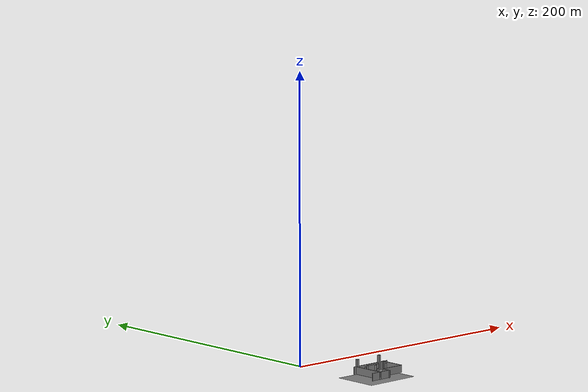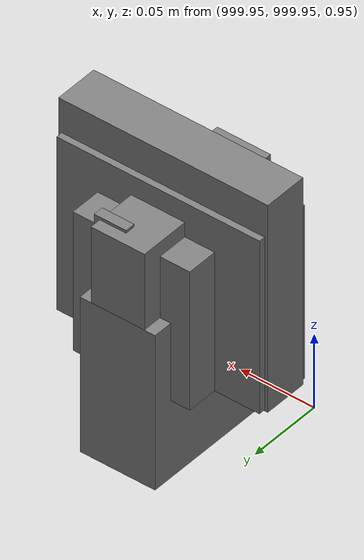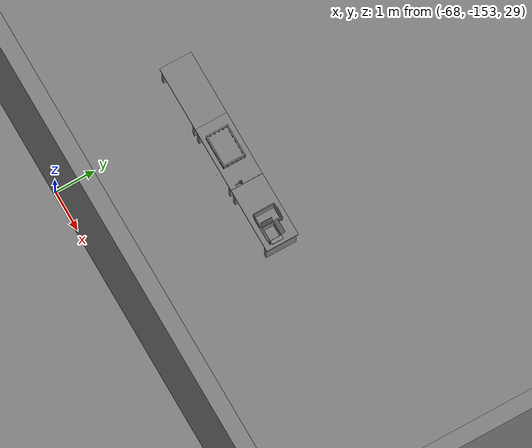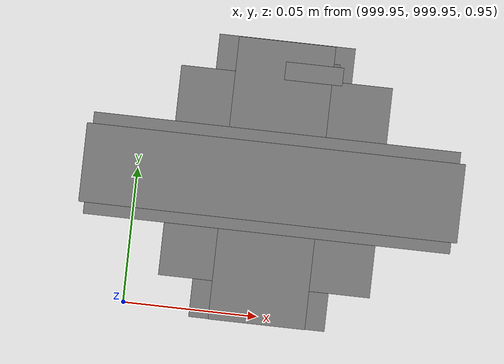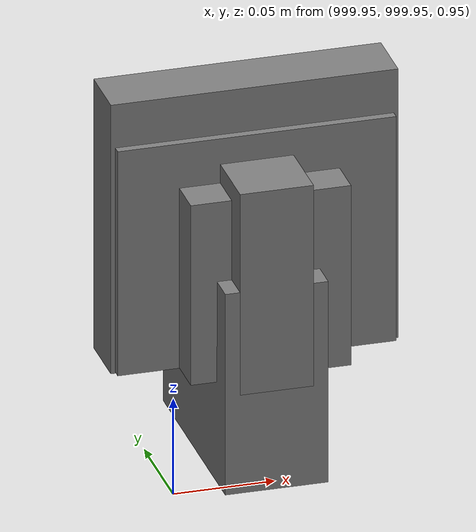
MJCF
<mujoco>
    <option gravity="0.000000000 0.000000000 -9.810000420" timestep="0.0049999999" integrator="implicitfast" density="1.225" viscosity="1.8000001e-05" noslip_iterations="10" iterations="100" sdf_iterations="50">
        <flag multiccd="disable"/>
    </option>
    <size memory="1000M"/>
    <compiler coordinate="local"/>
    <worldbody>
        <light cutoff="30" pos="0 1 1" dir="0 -1 -2"/>
        <light cutoff="30" pos="0 -1 1" dir="0 1 -2"/>
        <body pos="-64.866622925 -149.383972168 30.183746338" euler="89.999984741 89.999946594 0.000000000" name="openloong_gripper_2f85_fix_base_usda_bluebox_01">
            <geom contype="1" conaffinity="1" density="1000" type="box" material="" rgba="0.500000000 0.500000000 0.500000000 1.000000000" solimp="0.899999976 0.949999988 0.001000000" friction="1.000000000 0.005000000 0.000100000" solref="0.020000000 1.000000000" margin="0" condim="3" group="0" pos="0.276580811 0.187225342 0.000068665" quat="0.707106948 0.000077471 0.707106352 0.000077486" size="0.100000001 0.057999998 0.010000000" name="openloong_gripper_2f85_fix_base_usda_geom_6B2F3A71_E0C3_4B3E_8ED7_76C317D54AC7"/>
            <geom contype="1" conaffinity="1" density="1000" type="box" material="" rgba="0.500000000 0.500000000 0.500000000 1.000000000" solimp="0.899999976 0.949999988 0.001000000" friction="1.000000000 0.005000000 0.000100000" solref="0.020000000 1.000000000" margin="0" condim="3" group="0" pos="0.000000000 0.002883911 0.000000000" quat="0.999999881 0.000000000 0.000000000 0.000000000" size="0.254000008 0.003000000 0.172000006" name="openloong_gripper_2f85_fix_base_usda_geom_67192614_1A7E_4E1C_87DD_3F46366224CE"/>
            <geom contype="1" conaffinity="1" density="1000" type="box" material="" rgba="0.500000000 0.500000000 0.500000000 1.000000000" solimp="0.899999976 0.949999988 0.001000000" friction="1.000000000 0.005000000 0.000100000" solref="0.020000000 1.000000000" margin="0" condim="3" group="0" pos="0.000000000 0.124874115 0.173484802" quat="0.999796331 0.020176515 -0.000000015 0.000000030" size="0.259999990 0.119999997 0.007000000" name="openloong_gripper_2f85_fix_base_usda_geom_195F2A6D_6142_46D0_9FBE_AE68A6D9EF85"/>
            <geom contype="1" conaffinity="1" density="1000" type="box" material="" rgba="0.500000000 0.500000000 0.500000000 1.000000000" solimp="0.899999976 0.949999988 0.001000000" friction="1.000000000 0.005000000 0.000100000" solref="0.020000000 1.000000000" margin="0" condim="3" group="0" pos="0.000000000 0.124874115 -0.173469543" quat="0.999796331 -0.020176545 -0.000000015 0.000000000" size="0.259999990 0.119999997 0.007000000" name="openloong_gripper_2f85_fix_base_usda_geom_7D637C0A_FDD3_42E8_B0B8_BD42157AB527"/>
            <geom contype="1" conaffinity="1" density="1000" type="box" material="" rgba="0.500000000 0.500000000 0.500000000 1.000000000" solimp="0.899999976 0.949999988 0.001000000" friction="1.000000000 0.005000000 0.000100000" solref="0.020000000 1.000000000" margin="0" condim="3" group="0" pos="0.000000000 0.214008331 0.188980103" quat="0.999912977 0.013176724 0.000000015 0.000000000" size="0.259999990 0.029999999 0.012500000" name="openloong_gripper_2f85_fix_base_usda_geom_C5F56D52_6618_4834_B7F8_723E98B753A6"/>
            <geom contype="1" conaffinity="1" density="1000" type="box" material="" rgba="0.500000000 0.500000000 0.500000000 1.000000000" solimp="0.899999976 0.949999988 0.001000000" friction="1.000000000 0.005000000 0.000100000" solref="0.020000000 1.000000000" margin="0" condim="3" group="0" pos="-0.258361816 0.125289917 0.001876831" quat="0.702796936 -0.020792112 0.710783124 0.020769298" size="0.189999998 0.119999997 0.009000000" name="openloong_gripper_2f85_fix_base_usda_geom_D1EAF398_B1C6_41F7_8F9E_2D5096F6AEBE"/>
            <geom contype="1" conaffinity="1" density="1000" type="box" material="" rgba="0.500000000 0.500000000 0.500000000 1.000000000" solimp="0.899999976 0.949999988 0.001000000" friction="1.000000000 0.005000000 0.000100000" solref="0.020000000 1.000000000" margin="0" condim="3" group="0" pos="0.000000000 0.214008331 -0.188980103" quat="0.999912977 -0.013176769 0.000000030 0.000000015" size="0.259999990 0.029999999 0.012500000" name="openloong_gripper_2f85_fix_base_usda_geom_3B658031_FDE1_45AA_BEA6_85ADEC6F26C7"/>
            <geom contype="1" conaffinity="1" density="1000" type="box" material="" rgba="0.500000000 0.500000000 0.500000000 1.000000000" solimp="0.899999976 0.949999988 0.001000000" friction="1.000000000 0.005000000 0.000100000" solref="0.020000000 1.000000000" margin="0" condim="3" group="0" pos="-0.276611328 0.187225342 0.000068665" quat="0.707106650 0.000077441 0.707106709 0.000077456" size="0.100000001 0.057999998 0.010000000" name="openloong_gripper_2f85_fix_base_usda_geom_0648644F_187D_4333_964F_7DF327E55945"/>
            <geom contype="1" conaffinity="1" density="1000" type="box" material="" rgba="0.500000000 0.500000000 0.500000000 1.000000000" solimp="0.899999976 0.949999988 0.001000000" friction="1.000000000 0.005000000 0.000100000" solref="0.020000000 1.000000000" margin="0" condim="3" group="0" pos="0.258331299 0.125289917 0.001876831" quat="0.702851415 0.018856421 0.710823774 -0.019329369" size="0.189999998 0.119999997 0.009000000" name="openloong_gripper_2f85_fix_base_usda_geom_075326A3_6C26_4344_927B_36E0D4468533"/>
            <freejoint name="openloong_gripper_2f85_fix_base_usda_bluebox_01_joint"/>
            <site size="0.005000000 0.005000000 0.005000000" rgba="0.500000000 0.500000000 0.500000000 1.000000000" pos="0.000000000 0.000000000 0.000000000" quat="0.999961913 0.008726534 0.000000000 0.000000000" group="0" type="sphere" name="openloong_gripper_2f85_fix_base_usda_bluebox_01site"/>
        </body>
        <body pos="-64.496299744 -149.491867065 30.235729218" euler="0.000000000 0.000000000 89.999946594" name="openloong_gripper_2f85_fix_base_usda_cardboardbox_01">
            <geom contype="1" conaffinity="1" density="1000" type="box" material="" rgba="0.500000000 0.500000000 0.500000000 1.000000000" solimp="0.899999976 0.949999988 0.001000000" friction="1.000000000 0.005000000 0.000100000" solref="0.020000000 1.000000000" margin="0" condim="3" group="0" pos="-0.003166199 -0.004086494 0.005052090" quat="1.000000000 0.000000000 0.000000000 0.000000000" size="0.142499998 0.177500010 0.005000000" name="openloong_gripper_2f85_fix_base_usda_geom_98879CE3_5548_4E37_8D1E_344C65483EEA"/>
            <geom contype="1" conaffinity="1" density="1000" type="box" material="" rgba="0.500000000 0.500000000 0.500000000 1.000000000" solimp="0.899999976 0.949999988 0.001000000" friction="1.000000000 0.005000000 0.000100000" solref="0.020000000 1.000000000" margin="0" condim="3" group="0" pos="-0.003166199 0.170316696 0.150570869" quat="1.000000000 0.000000000 0.000000000 0.000000000" size="0.142499998 0.005000000 0.149999991" name="openloong_gripper_2f85_fix_base_usda_geom_89BBE757_BD43_4E74_9175_C66ED4DA4955"/>
            <geom contype="1" conaffinity="1" density="1000" type="box" material="" rgba="0.500000000 0.500000000 0.500000000 1.000000000" solimp="0.899999976 0.949999988 0.001000000" friction="1.000000000 0.005000000 0.000100000" solref="0.020000000 1.000000000" margin="0" condim="3" group="0" pos="-0.147399902 -0.005307198 0.150570869" quat="1.000000000 0.000000000 0.000000000 0.000000000" size="0.005000000 0.177500010 0.149999991" name="openloong_gripper_2f85_fix_base_usda_geom_FC36B775_5B66_495D_B0E0_7CEF5A621604"/>
            <geom contype="1" conaffinity="1" density="1000" type="box" material="" rgba="0.500000000 0.500000000 0.500000000 1.000000000" solimp="0.899999976 0.949999988 0.001000000" friction="1.000000000 0.005000000 0.000100000" solref="0.020000000 1.000000000" margin="0" condim="3" group="0" pos="0.140275955 -0.005307198 0.150570869" quat="1.000000000 0.000000000 0.000000000 0.000000000" size="0.005000000 0.177500010 0.149999991" name="openloong_gripper_2f85_fix_base_usda_geom_5FCE39F4_0D85_4335_8997_C6C3AABA534C"/>
            <geom contype="1" conaffinity="1" density="1000" type="box" material="" rgba="0.500000000 0.500000000 0.500000000 1.000000000" solimp="0.899999976 0.949999988 0.001000000" friction="1.000000000 0.005000000 0.000100000" solref="0.020000000 1.000000000" margin="0" condim="3" group="0" pos="-0.003166199 -0.181550980 0.150570869" quat="1.000000000 0.000000000 0.000000000 0.000000000" size="0.142499998 0.005000000 0.149999991" name="openloong_gripper_2f85_fix_base_usda_geom_4A22A296_92F0_4F35_8731_F6687FA72967"/>
            <freejoint name="openloong_gripper_2f85_fix_base_usda_cardboardbox_01_joint"/>
            <site size="0.005000000 0.005000000 0.005000000" rgba="0.500000000 0.500000000 0.500000000 1.000000000" pos="0.000000000 0.000000000 0.000000000" quat="0.999961913 0.008726535 0.000000000 0.000000000" group="0" type="sphere" name="openloong_gripper_2f85_fix_base_usda_site_0E92C566_0A3F_4D4E_8857_BD835C5A5B9F"/>
            <body pos="0.139160156 -0.004048347 0.301930904" euler="-179.999954224 49.383502960 179.999954224" name="openloong_gripper_2f85_fix_base_usda_A1_006">
                <geom contype="1" conaffinity="1" density="1000" type="box" material="" rgba="0.500000000 0.500000000 0.500000000 1.000000000" solimp="0.899999976 0.949999988 0.001000000" friction="1.000000000 0.005000000 0.000100000" solref="0.020000000 1.000000000" margin="0" condim="3" group="0" pos="-0.071587563 0.000009537 0.001745224" quat="0.999999881 0.000000000 0.000000000 0.000000000" size="0.071249999 0.179999992 0.002500000" name="openloong_gripper_2f85_fix_base_usda_geom_8E311C31_46BB_411E_9DB6_635C3F9532AE"/>
                <joint armature="0" stiffness="0.07" damping="0.0099999998" axis="0.000000 1.000000 0.000000" type="hinge" name="openloong_gripper_2f85_fix_base_usda_A1_006"/>
            </body>
            <body pos="-0.145902634 -0.004086494 0.301938057" euler="-180.000000000 -60.000011444 -180.000000000" name="openloong_gripper_2f85_fix_base_usda_A2_006">
                <geom contype="1" conaffinity="1" density="1000" type="box" material="" rgba="0.500000000 0.500000000 0.500000000 1.000000000" solimp="0.899999976 0.949999988 0.001000000" friction="1.000000000 0.005000000 0.000100000" solref="0.020000000 1.000000000" margin="0" condim="3" group="0" pos="0.071268082 0.000009537 0.002717972" quat="0.000002921 0.000000000 -0.000000030 0.999999881" size="0.071249999 0.179999992 0.002500000" name="openloong_gripper_2f85_fix_base_usda_geom_9F4DDFBF_05D5_4B06_B5DC_7A7D661AC944"/>
                <joint armature="0" stiffness="0.07" damping="0.0099999998" axis="0.000000 1.000000 0.000000" type="hinge" name="openloong_gripper_2f85_fix_base_usda_A2_006"/>
            </body>
            <body pos="-0.003385544 0.175991058 0.301930904" euler="-125.858116150 -0.000004561 0.000002331" name="openloong_gripper_2f85_fix_base_usda_B2_006">
                <geom contype="1" conaffinity="1" density="1000" type="box" material="" rgba="0.500000000 0.500000000 0.500000000 1.000000000" solimp="0.899999976 0.949999988 0.001000000" friction="1.000000000 0.005000000 0.000100000" solref="0.020000000 1.000000000" margin="0" condim="3" group="0" pos="0.000009537 -0.070939064 -0.002470016" quat="0.999614120 0.027776197 -0.000000015 0.000000030" size="0.137500003 0.064999998 0.005000000" name="openloong_gripper_2f85_fix_base_usda_geom_537D554A_0A49_4576_BBAC_2A9FDC92EB39"/>
                <joint armature="0" stiffness="0.07" damping="0.0099999998" axis="1.000000 0.000000 0.000000" type="hinge" name="openloong_gripper_2f85_fix_base_usda_B2_006"/>
            </body>
            <body pos="-0.003385544 -0.184140205 0.301938057" euler="147.805557251 0.000000000 0.000000000" name="openloong_gripper_2f85_fix_base_usda_B1_006">
                <geom contype="1" conaffinity="1" density="1000" type="box" material="" rgba="0.500000000 0.500000000 0.500000000 1.000000000" solimp="0.899999976 0.949999988 0.001000000" friction="1.000000000 0.005000000 0.000100000" solref="0.020000000 1.000000000" margin="0" condim="3" group="0" pos="-0.000028610 0.070202351 -0.002703667" quat="0.999614179 -0.027776167 0.000000000 0.000000000" size="0.137500003 0.064999998 0.005000000" name="openloong_gripper_2f85_fix_base_usda_geom_8BE7723D_601A_4C3B_B04A_374EC9E37156"/>
                <joint armature="0" stiffness="0.07" damping="0.0099999998" axis="1.000000 0.000000 0.000000" type="hinge" name="openloong_gripper_2f85_fix_base_usda_B1_006"/>
            </body>
        </body>
        <body pos="-65.882858276 -149.481979370 30.229999542" euler="-64.487716675 0.000000000 0.000000000" name="openloong_gripper_2f85_fix_base_usda_Barcode">
            <geom contype="1" conaffinity="1" density="1000" type="box" material="" rgba="0.500000000 0.500000000 0.500000000 1.000000000" solimp="0.899999976 0.949999988 0.001000000" friction="1.000000000 0.005000000 0.000100000" solref="0.020000000 1.000000000" margin="0" condim="3" group="0" pos="0.000000000 0.013038635 0.001419067" quat="0.000000000 0.000000000 0.000000000 1.000000119" size="0.034000002 0.010000000 0.017999999" name="openloong_gripper_2f85_fix_base_usda_geom_5D8BF100_D90A_450F_B14E_00B3B5039E69"/>
            <geom contype="1" conaffinity="1" density="1000" type="box" material="" rgba="0.500000000 0.500000000 0.500000000 1.000000000" solimp="0.899999976 0.949999988 0.001000000" friction="1.000000000 0.005000000 0.000100000" solref="0.020000000 1.000000000" margin="0" condim="3" group="0" pos="0.000000000 -0.035301208 -0.007095337" quat="0.000000000 0.000000000 -0.043619365 0.999048233" size="0.028999999 0.010000000 0.020000000" name="openloong_gripper_2f85_fix_base_usda_geom_45249E8B_69B2_4874_BF82_E44F65239412"/>
            <geom contype="1" conaffinity="1" density="1000" type="box" material="" rgba="0.500000000 0.500000000 0.500000000 1.000000000" solimp="0.899999976 0.949999988 0.001000000" friction="1.000000000 0.005000000 0.000100000" solref="0.020000000 1.000000000" margin="0" condim="3" group="0" pos="0.000000000 -0.043411255 -0.011749268" quat="0.922262907 0.386563420 0.000000000 0.000000000" size="0.026000001 0.010000000 0.020000000" name="openloong_gripper_2f85_fix_base_usda_geom_D08AF65C_2F5F_4D29_B4CE_25B7CC51F348"/>
            <geom contype="1" conaffinity="1" density="1000" type="box" material="" rgba="0.500000000 0.500000000 0.500000000 1.000000000" solimp="0.899999976 0.949999988 0.001000000" friction="1.000000000 0.005000000 0.000100000" solref="0.020000000 1.000000000" margin="0" condim="3" group="0" pos="0.000000000 -0.016967773 -0.031860352" quat="0.000000000 0.000000000 0.000000000 1.000000119" size="0.008000000 0.010000000 0.013000000" name="openloong_gripper_2f85_fix_base_usda_geom_C1EFB7B0_775F_4139_BE7B_0A7F4ECF0D0D"/>
            <geom contype="1" conaffinity="1" density="1000" type="box" material="" rgba="0.500000000 0.500000000 0.500000000 1.000000000" solimp="0.899999976 0.949999988 0.001000000" friction="1.000000000 0.005000000 0.000100000" solref="0.020000000 1.000000000" margin="0" condim="3" group="0" pos="0.000000000 -0.001869202 0.000312805" quat="0.953716993 0.300705761 0.000000000 0.000000000" size="0.032000002 0.010000000 0.018999999" name="openloong_gripper_2f85_fix_base_usda_geom_FB45458E_6CFC_4AF0_85E5_637BDD2D37A8"/>
            <geom contype="1" conaffinity="1" density="1000" type="box" material="" rgba="0.500000000 0.500000000 0.500000000 1.000000000" solimp="0.899999976 0.949999988 0.001000000" friction="1.000000000 0.005000000 0.000100000" solref="0.020000000 1.000000000" margin="0" condim="3" group="0" pos="0.000000000 -0.019531250 -0.003173828" quat="0.953716993 0.300705761 0.000000000 0.000000000" size="0.030999999 0.010000000 0.020000000" name="openloong_gripper_2f85_fix_base_usda_geom_24BB89EC_FDA2_4733_8414_B0E7EC8964C9"/>
            <geom contype="1" conaffinity="1" density="1000" type="box" material="" rgba="0.500000000 0.500000000 0.500000000 1.000000000" solimp="0.899999976 0.949999988 0.001000000" friction="1.000000000 0.005000000 0.000100000" solref="0.020000000 1.000000000" margin="0" condim="3" group="0" pos="0.000000000 -0.035301208 -0.007095337" quat="0.953716993 0.300705761 0.000000000 0.000000000" size="0.028999999 0.010000000 0.020000000" name="openloong_gripper_2f85_fix_base_usda_geom_E587011C_1055_42EC_B489_45AD63B28588"/>
            <geom contype="1" conaffinity="1" density="1000" type="box" material="" rgba="0.500000000 0.500000000 0.500000000 1.000000000" solimp="0.899999976 0.949999988 0.001000000" friction="1.000000000 0.005000000 0.000100000" solref="0.020000000 1.000000000" margin="0" condim="3" group="0" pos="0.000000000 -0.042617798 -0.071121216" quat="0.000000000 0.000000000 0.000000000 1.000000119" size="0.013000000 0.021000000 0.059999999" name="openloong_gripper_2f85_fix_base_usda_geom_5D5F9EF2_2A70_4A9D_9F4F_0BD89553508E"/>
            <freejoint name="openloong_gripper_2f85_fix_base_usda_Barcode_joint"/>
            <site size="0.005000000 0.005000000 0.005000000" rgba="0.500000000 0.500000000 0.500000000 1.000000000" pos="0.000000000 0.000000000 0.000000000" quat="1.000000000 0.000000000 0.000000000 0.000000000" group="0" type="sphere" name="openloong_gripper_2f85_fix_base_usda_Barcode_site"/>
        </body>
        <body pos="-66.745018005 -149.392349243 30.184000015" euler="0.000000000 0.000000000 89.999946594" name="[22332490611815]_Basket_01">
            <geom contype="1" conaffinity="1" density="1000" type="box" material="" rgba="0.500000000 0.500000000 0.500000000 1.000000000" solimp="0.899999976 0.949999988 0.001000000" friction="1.000000000 0.005000000 0.000100000" solref="0.020000000 1.000000000" margin="0" condim="3" group="0" pos="-0.052425385 0.389207840 0.089787483" quat="0.707107008 0.000000000 0.000000000 0.707106411" size="0.014249999 0.014249999 0.059999999" name="[22332490611815]_geom_3EE272F3_A0D8_4DA2_8ACD_795FE79C28AB"/>
            <geom contype="1" conaffinity="1" density="1000" type="box" material="" rgba="0.500000000 0.500000000 0.500000000 1.000000000" solimp="0.899999976 0.949999988 0.001000000" friction="1.000000000 0.005000000 0.000100000" solref="0.020000000 1.000000000" margin="0" condim="3" group="0" pos="0.264015198 -0.133043289 0.089787483" quat="0.707107008 0.000000000 0.000000000 0.707106411" size="0.014249999 0.014249999 0.059999999" name="[22332490611815]_geom_44897FD6_3D89_4E1B_90BA_1A32CC42DB27"/>
            <geom contype="1" conaffinity="1" density="1000" type="box" material="" rgba="0.500000000 0.500000000 0.500000000 1.000000000" solimp="0.899999976 0.949999988 0.001000000" friction="1.000000000 0.005000000 0.000100000" solref="0.020000000 1.000000000" margin="0" condim="3" group="0" pos="-0.264015198 -0.265548706 0.089793205" quat="0.707107008 0.000000000 0.000000000 0.707106411" size="0.014249999 0.014249999 0.059999999" name="[22332490611815]_geom_3E92908F_6472_4DEC_B437_4B5F680A3F52"/>
            <geom contype="1" conaffinity="1" density="1000" type="box" material="" rgba="0.500000000 0.500000000 0.500000000 1.000000000" solimp="0.899999976 0.949999988 0.001000000" friction="1.000000000 0.005000000 0.000100000" solref="0.020000000 1.000000000" margin="0" condim="3" group="0" pos="-0.160263062 -0.389322281 0.089793205" quat="0.707107008 0.000000000 0.000000000 0.707106411" size="0.014249999 0.014249999 0.059999999" name="[22332490611815]_geom_F2B39E3E_047A_4005_80E5_BDA557E1F3EB"/>
            <geom contype="1" conaffinity="1" density="1000" type="box" material="" rgba="0.500000000 0.500000000 0.500000000 1.000000000" solimp="0.899999976 0.949999988 0.001000000" friction="1.000000000 0.005000000 0.000100000" solref="0.020000000 1.000000000" margin="0" condim="3" group="0" pos="0.162265778 -0.389322281 0.089787483" quat="0.707107008 0.000000000 0.000000000 0.707106411" size="0.014249999 0.014249999 0.059999999" name="[22332490611815]_geom_24A7B543_B9B9_4A4E_909C_2150B0741D3A"/>
            <geom contype="1" conaffinity="1" density="1000" type="box" material="" rgba="0.500000000 0.500000000 0.500000000 1.000000000" solimp="0.899999976 0.949999988 0.001000000" friction="1.000000000 0.005000000 0.000100000" solref="0.020000000 1.000000000" margin="0" condim="3" group="0" pos="0.264015198 0.389207840 0.089787483" quat="0.707107008 0.000000000 0.000000000 0.707106411" size="0.014249999 0.014249999 0.059999999" name="[22332490611815]_geom_6371B098_0B7B_438F_A74C_E0339C1862B4"/>
            <geom contype="1" conaffinity="1" density="1000" type="box" material="" rgba="0.500000000 0.500000000 0.500000000 1.000000000" solimp="0.899999976 0.949999988 0.001000000" friction="1.000000000 0.005000000 0.000100000" solref="0.020000000 1.000000000" margin="0" condim="3" group="0" pos="-0.264015198 -0.133043289 0.089793205" quat="0.707107008 0.000000000 0.000000000 0.707106411" size="0.014249999 0.014249999 0.059999999" name="[22332490611815]_geom_E17110F5_00AF_4547_97A3_71B0328ED7ED"/>
            <geom contype="1" conaffinity="1" density="1000" type="box" material="" rgba="0.500000000 0.500000000 0.500000000 1.000000000" solimp="0.899999976 0.949999988 0.001000000" friction="1.000000000 0.005000000 0.000100000" solref="0.020000000 1.000000000" margin="0" condim="3" group="0" pos="-0.264026642 0.269256592 0.089793205" quat="0.707107008 0.000000000 0.000000000 0.707106411" size="0.014249999 0.014249999 0.059999999" name="[22332490611815]_geom_91A8E60E_CB43_4163_B60F_96A69C979E72"/>
            <geom contype="1" conaffinity="1" density="1000" type="box" material="" rgba="0.500000000 0.500000000 0.500000000 1.000000000" solimp="0.899999976 0.949999988 0.001000000" friction="1.000000000 0.005000000 0.000100000" solref="0.020000000 1.000000000" margin="0" condim="3" group="0" pos="0.054462433 0.389207840 0.089787483" quat="0.707107008 0.000000000 0.000000000 0.707106411" size="0.014249999 0.014249999 0.059999999" name="[22332490611815]_geom_E325B2B5_3D55_43FA_A6FF_C8C8DDD60576"/>
            <geom contype="1" conaffinity="1" density="1000" type="box" material="" rgba="0.500000000 0.500000000 0.500000000 1.000000000" solimp="0.899999976 0.949999988 0.001000000" friction="1.000000000 0.005000000 0.000100000" solref="0.020000000 1.000000000" margin="0" condim="3" group="0" pos="0.054462433 -0.389322281 0.089787483" quat="0.707107008 0.000000000 0.000000000 0.707106411" size="0.014249999 0.014249999 0.059999999" name="[22332490611815]_geom_07B9C93C_8484_4D8C_BFE3_92767A7B7072"/>
            <geom contype="1" conaffinity="1" density="1000" type="box" material="" rgba="0.500000000 0.500000000 0.500000000 1.000000000" solimp="0.899999976 0.949999988 0.001000000" friction="1.000000000 0.005000000 0.000100000" solref="0.020000000 1.000000000" margin="0" condim="3" group="0" pos="0.264015198 0.269256592 0.089793205" quat="0.707107008 0.000000000 0.000000000 0.707106411" size="0.014249999 0.014249999 0.059999999" name="[22332490611815]_geom_3BFE76AF_0EF5_469B_A64B_EF850804BFE2"/>
            <geom contype="1" conaffinity="1" density="1000" type="box" material="" rgba="0.500000000 0.500000000 0.500000000 1.000000000" solimp="0.899999976 0.949999988 0.001000000" friction="1.000000000 0.005000000 0.000100000" solref="0.020000000 1.000000000" margin="0" condim="3" group="0" pos="0.264015198 -0.389322281 0.089787483" quat="0.707107008 0.000000000 0.000000000 0.707106411" size="0.014249999 0.014249999 0.059999999" name="[22332490611815]_geom_177F6E22_9B3B_492B_911A_8BAAD1B351A3"/>
            <geom contype="1" conaffinity="1" density="1000" type="box" material="" rgba="0.500000000 0.500000000 0.500000000 1.000000000" solimp="0.899999976 0.949999988 0.001000000" friction="1.000000000 0.005000000 0.000100000" solref="0.020000000 1.000000000" margin="0" condim="3" group="0" pos="0.000000000 0.000000000 0.015998840" quat="0.707107008 0.000000000 0.000000000 0.707106411" size="0.403499991 0.279000014 0.015750000" name="[22332490611815]_geom_017E42E3_C6E8_46AF_B725_19D38396B4FC"/>
            <geom contype="1" conaffinity="1" density="1000" type="box" material="" rgba="0.500000000 0.500000000 0.500000000 1.000000000" solimp="0.899999976 0.949999988 0.001000000" friction="1.000000000 0.005000000 0.000100000" solref="0.020000000 1.000000000" margin="0" condim="3" group="0" pos="0.000000000 -0.389476776 0.163619041" quat="0.707107008 0.000000000 0.000000000 0.707106411" size="0.015000000 0.277500004 0.015750000" name="[22332490611815]_geom_FB452278_A1BD_4381_BAAE_159F495BFCDD"/>
            <geom contype="1" conaffinity="1" density="1000" type="box" material="" rgba="0.500000000 0.500000000 0.500000000 1.000000000" solimp="0.899999976 0.949999988 0.001000000" friction="1.000000000 0.005000000 0.000100000" solref="0.020000000 1.000000000" margin="0" condim="3" group="0" pos="0.162265778 0.389207840 0.089787483" quat="0.707107008 0.000000000 0.000000000 0.707106411" size="0.014249999 0.014249999 0.059999999" name="[22332490611815]_geom_B5CC9E58_03BE_4D94_9FDC_B80EEBF50BD0"/>
            <geom contype="1" conaffinity="1" density="1000" type="box" material="" rgba="0.500000000 0.500000000 0.500000000 1.000000000" solimp="0.899999976 0.949999988 0.001000000" friction="1.000000000 0.005000000 0.000100000" solref="0.020000000 1.000000000" margin="0" condim="3" group="0" pos="0.000000000 0.389471054 0.163619041" quat="0.707107008 0.000000000 0.000000000 0.707106411" size="0.015000000 0.277500004 0.015750000" name="[22332490611815]_geom_ECE77AEC_D490_45FB_976F_2B10B2CC9F5A"/>
            <geom contype="1" conaffinity="1" density="1000" type="box" material="" rgba="0.500000000 0.500000000 0.500000000 1.000000000" solimp="0.899999976 0.949999988 0.001000000" friction="1.000000000 0.005000000 0.000100000" solref="0.020000000 1.000000000" margin="0" condim="3" group="0" pos="-0.263511658 0.000000000 0.163619041" quat="0.707107008 0.000000000 0.000000000 0.707106411" size="0.403499991 0.015000000 0.015750000" name="[22332490611815]_geom_7B74E51E_74AA_49A2_B26B_A98BAB704A61"/>
            <geom contype="1" conaffinity="1" density="1000" type="box" material="" rgba="0.500000000 0.500000000 0.500000000 1.000000000" solimp="0.899999976 0.949999988 0.001000000" friction="1.000000000 0.005000000 0.000100000" solref="0.020000000 1.000000000" margin="0" condim="3" group="0" pos="-0.264015198 0.141334534 0.089793205" quat="0.707107008 0.000000000 0.000000000 0.707106411" size="0.014249999 0.014249999 0.059999999" name="[22332490611815]_geom_F909E6D0_0329_4FEF_83AC_775FE2A6D441"/>
            <geom contype="1" conaffinity="1" density="1000" type="box" material="" rgba="0.500000000 0.500000000 0.500000000 1.000000000" solimp="0.899999976 0.949999988 0.001000000" friction="1.000000000 0.005000000 0.000100000" solref="0.020000000 1.000000000" margin="0" condim="3" group="0" pos="0.264015198 -0.265548706 0.089787483" quat="0.707107008 0.000000000 0.000000000 0.707106411" size="0.014249999 0.014249999 0.059999999" name="[22332490611815]_geom_71E6695D_E5E3_4DBB_A33F_9528B613AB39"/>
            <geom contype="1" conaffinity="1" density="1000" type="box" material="" rgba="0.500000000 0.500000000 0.500000000 1.000000000" solimp="0.899999976 0.949999988 0.001000000" friction="1.000000000 0.005000000 0.000100000" solref="0.020000000 1.000000000" margin="0" condim="3" group="0" pos="-0.160263062 0.389207840 0.089787483" quat="0.707107008 0.000000000 0.000000000 0.707106411" size="0.014249999 0.014249999 0.059999999" name="[22332490611815]_geom_DC2BEE25_74E6_47BA_811E_F4FF292075CC"/>
            <geom contype="1" conaffinity="1" density="1000" type="box" material="" rgba="0.500000000 0.500000000 0.500000000 1.000000000" solimp="0.899999976 0.949999988 0.001000000" friction="1.000000000 0.005000000 0.000100000" solref="0.020000000 1.000000000" margin="0" condim="3" group="0" pos="-0.052425385 -0.389322281 0.089787483" quat="0.707107008 0.000000000 0.000000000 0.707106411" size="0.014249999 0.014249999 0.059999999" name="[22332490611815]_geom_F850D024_448C_47B1_AEE3_D5F42D167904"/>
            <geom contype="1" conaffinity="1" density="1000" type="box" material="" rgba="0.500000000 0.500000000 0.500000000 1.000000000" solimp="0.899999976 0.949999988 0.001000000" friction="1.000000000 0.005000000 0.000100000" solref="0.020000000 1.000000000" margin="0" condim="3" group="0" pos="-0.264026642 -0.389322281 0.089793205" quat="0.707107008 0.000000000 0.000000000 0.707106411" size="0.014249999 0.014249999 0.059999999" name="[22332490611815]_geom_1E1EE7AC_00CA_4109_A228_5F9247BCC5A2"/>
            <geom contype="1" conaffinity="1" density="1000" type="box" material="" rgba="0.500000000 0.500000000 0.500000000 1.000000000" solimp="0.899999976 0.949999988 0.001000000" friction="1.000000000 0.005000000 0.000100000" solref="0.020000000 1.000000000" margin="0" condim="3" group="0" pos="0.264015198 0.141334534 0.089787483" quat="0.707107008 0.000000000 0.000000000 0.707106411" size="0.014249999 0.014249999 0.059999999" name="[22332490611815]_geom_AA7AACE2_4B6B_487A_96B5_4AC7F0C63FDF"/>
            <geom contype="1" conaffinity="1" density="1000" type="box" material="" rgba="0.500000000 0.500000000 0.500000000 1.000000000" solimp="0.899999976 0.949999988 0.001000000" friction="1.000000000 0.005000000 0.000100000" solref="0.020000000 1.000000000" margin="0" condim="3" group="0" pos="-0.264015198 0.389207840 0.089793205" quat="0.707107008 0.000000000 0.000000000 0.707106411" size="0.014249999 0.014249999 0.059999999" name="[22332490611815]_geom_0BE0614F_71EF_4D8C_87F8_536983697112"/>
            <geom contype="1" conaffinity="1" density="1000" type="box" material="" rgba="0.500000000 0.500000000 0.500000000 1.000000000" solimp="0.899999976 0.949999988 0.001000000" friction="1.000000000 0.005000000 0.000100000" solref="0.020000000 1.000000000" margin="0" condim="3" group="0" pos="0.264015198 0.004480362 0.089787483" quat="0.707107008 0.000000000 0.000000000 0.707106411" size="0.014249999 0.014249999 0.059999999" name="[22332490611815]_geom_5AAF3382_BA0E_446A_B825_080244F1EE26"/>
            <geom contype="1" conaffinity="1" density="1000" type="box" material="" rgba="0.500000000 0.500000000 0.500000000 1.000000000" solimp="0.899999976 0.949999988 0.001000000" friction="1.000000000 0.005000000 0.000100000" solref="0.020000000 1.000000000" margin="0" condim="3" group="0" pos="0.263694763 -0.000011444 0.163619041" quat="0.707107008 0.000000000 0.000000000 0.707106411" size="0.403499991 0.015000000 0.015750000" name="[22332490611815]_geom_C875A9AD_4F54_4667_802E_CE7360F4ABA2"/>
            <geom contype="1" conaffinity="1" density="1000" type="box" material="" rgba="0.500000000 0.500000000 0.500000000 1.000000000" solimp="0.899999976 0.949999988 0.001000000" friction="1.000000000 0.005000000 0.000100000" solref="0.020000000 1.000000000" margin="0" condim="3" group="0" pos="-0.264015198 0.004480362 0.089793205" quat="0.707107008 0.000000000 0.000000000 0.707106411" size="0.014249999 0.014249999 0.059999999" name="[22332490611815]_geom_8ECCFEB2_8ABD_4D10_B9A0_66C87565F477"/>
            <freejoint name="[22332490611815]_joint_7DB20B74_9234_4DDE_8F78_D57229F167A7"/>
        </body>
        <body pos="0.000000000 0.000000000 0.000000000" euler="0.000000000 0.000000000 0.000000000" name="Static Objects_Static Objects">
            <geom contype="1" conaffinity="1" density="1000" type="box" material="" rgba="0.500000000 0.500000000 0.500000000 1.000000000" solimp="0.899999976 0.949999988 0.001000000" friction="1.000000000 0.005000000 0.000100000" solref="0.020000000 1.000000000" margin="0" condim="3" group="0" pos="-67.544113159 -149.365814209 29.727830887" quat="0.500000417 0.499999970 0.499999553 0.499999970" size="0.381000012 0.319999993 0.041000001" name="Static Objects_geom_6D305708_36A8_462C_AF5D_D788011D7A98"/>
            <geom contype="1" conaffinity="1" density="1000" type="box" material="" rgba="0.500000000 0.500000000 0.500000000 1.000000000" solimp="0.899999976 0.949999988 0.001000000" friction="1.000000000 0.005000000 0.000100000" solref="0.020000000 1.000000000" margin="0" condim="3" group="0" pos="-68.239501953 -149.365814209 30.086868286" quat="0.500000417 0.499999970 0.499999553 0.499999970" size="0.370999992 0.039500002 0.745000005" name="Static Objects_geom_4D91CFC9_6829_402C_9050_0F6573BB4533"/>
            <geom contype="1" conaffinity="1" density="1000" type="box" material="" rgba="0.500000000 0.500000000 0.500000000 1.000000000" solimp="0.899999976 0.949999988 0.001000000" friction="1.000000000 0.005000000 0.000100000" solref="0.020000000 1.000000000" margin="0" condim="3" group="0" pos="-68.239501953 -149.365814209 30.147235870" quat="0.500000417 0.499999970 0.499999553 0.499999970" size="0.400000006 0.022000000 0.800000012" name="Static Objects_geom_0B08BD29_FDAC_47AA_BB88_A97599ACC970"/>
            <geom contype="1" conaffinity="1" density="1000" type="box" material="" rgba="0.500000000 0.500000000 0.500000000 1.000000000" solimp="0.899999976 0.949999988 0.001000000" friction="1.000000000 0.005000000 0.000100000" solref="0.020000000 1.000000000" margin="0" condim="3" group="0" pos="-68.934890747 -149.365814209 29.727830887" quat="0.500000417 0.499999970 0.499999553 0.499999970" size="0.381000012 0.319999993 0.041000001" name="Static Objects_geom_F16A177E_0A9F_4617_B624_F1679E146F64"/>
            <geom contype="1" conaffinity="1" density="1000" type="box" material="" rgba="0.500000000 0.500000000 0.500000000 1.000000000" solimp="0.899999976 0.949999988 0.001000000" friction="1.000000000 0.005000000 0.000100000" solref="0.020000000 1.000000000" margin="0" condim="3" group="0" pos="-68.239501953 -149.365814209 29.561563492" quat="0.500000417 0.499999970 0.499999553 0.499999970" size="0.020000000 0.022000000 0.660000026" name="Static Objects_geom_D05C6DD5_E333_48CC_850D_0600897B0F6F"/>
            <geom contype="1" conaffinity="1" density="1000" type="box" material="" rgba="0.500000000 0.500000000 0.500000000 1.000000000" solimp="0.899999976 0.949999988 0.001000000" friction="1.000000000 0.005000000 0.000100000" solref="0.020000000 1.000000000" margin="0" condim="3" group="0" pos="-65.945671082 -149.365814209 29.727830887" quat="0.500000417 0.499999970 0.499999553 0.499999970" size="0.381000012 0.319999993 0.041000001" name="Static Objects_geom_95A2096D_95C8_4626_8582_560D181D15E2"/>
            <geom contype="1" conaffinity="1" density="1000" type="box" material="" rgba="0.500000000 0.500000000 0.500000000 1.000000000" solimp="0.899999976 0.949999988 0.001000000" friction="1.000000000 0.005000000 0.000100000" solref="0.020000000 1.000000000" margin="0" condim="3" group="0" pos="-66.641059875 -149.365814209 30.086868286" quat="0.500000417 0.499999970 0.499999553 0.499999970" size="0.370999992 0.039500002 0.745000005" name="Static Objects_geom_5F01FA72_C346_44FF_BE28_30285C41997C"/>
            <geom contype="1" conaffinity="1" density="1000" type="box" material="" rgba="0.500000000 0.500000000 0.500000000 1.000000000" solimp="0.899999976 0.949999988 0.001000000" friction="1.000000000 0.005000000 0.000100000" solref="0.020000000 1.000000000" margin="0" condim="3" group="0" pos="-66.641059875 -149.365814209 30.147235870" quat="0.500000417 0.499999970 0.499999553 0.499999970" size="0.400000006 0.022000000 0.800000012" name="Static Objects_geom_88BDBFA7_5E69_4166_8EAB_C83D320C6F04"/>
            <geom contype="1" conaffinity="1" density="1000" type="box" material="" rgba="0.500000000 0.500000000 0.500000000 1.000000000" solimp="0.899999976 0.949999988 0.001000000" friction="1.000000000 0.005000000 0.000100000" solref="0.020000000 1.000000000" margin="0" condim="3" group="0" pos="-67.336448669 -149.365814209 29.727830887" quat="0.500000417 0.499999970 0.499999553 0.499999970" size="0.381000012 0.319999993 0.041000001" name="Static Objects_geom_A1D3F5A0_A0E4_409A_BEE4_4C2200108D9C"/>
            <geom contype="1" conaffinity="1" density="1000" type="box" material="" rgba="0.500000000 0.500000000 0.500000000 1.000000000" solimp="0.899999976 0.949999988 0.001000000" friction="1.000000000 0.005000000 0.000100000" solref="0.020000000 1.000000000" margin="0" condim="3" group="0" pos="-66.641059875 -149.365814209 29.561563492" quat="0.500000417 0.499999970 0.499999553 0.499999970" size="0.020000000 0.022000000 0.660000026" name="Static Objects_geom_4064EFA3_90C9_4C9C_9D43_4A5CFAC04977"/>
            <geom contype="1" conaffinity="1" density="1000" type="box" material="" rgba="0.500000000 0.500000000 0.500000000 1.000000000" solimp="0.899999976 0.949999988 0.001000000" friction="1.000000000 0.005000000 0.000100000" solref="0.020000000 1.000000000" margin="0" condim="3" group="0" pos="-64.338577271 -149.365814209 29.727830887" quat="0.500000417 0.499999970 0.499999553 0.499999970" size="0.381000012 0.319999993 0.041000001" name="Static Objects_geom_66937C80_5960_44BC_8D0B_2686ACFA86D9"/>
            <geom contype="1" conaffinity="1" density="1000" type="box" material="" rgba="0.500000000 0.500000000 0.500000000 1.000000000" solimp="0.899999976 0.949999988 0.001000000" friction="1.000000000 0.005000000 0.000100000" solref="0.020000000 1.000000000" margin="0" condim="3" group="0" pos="-65.033966064 -149.365814209 30.086868286" quat="0.500000417 0.499999970 0.499999553 0.499999970" size="0.370999992 0.039500002 0.745000005" name="Static Objects_geom_DA43055A_F797_44A6_8C8D_AB949494EAF5"/>
            <geom contype="1" conaffinity="1" density="1000" type="box" material="" rgba="0.500000000 0.500000000 0.500000000 1.000000000" solimp="0.899999976 0.949999988 0.001000000" friction="1.000000000 0.005000000 0.000100000" solref="0.020000000 1.000000000" margin="0" condim="3" group="0" pos="-65.033966064 -149.365814209 30.147235870" quat="0.500000417 0.499999970 0.499999553 0.499999970" size="0.400000006 0.022000000 0.800000012" name="Static Objects_geom_61FDF90F_E5E3_4C22_AE1D_9ABF851D2CAB"/>
            <geom contype="1" conaffinity="1" density="1000" type="box" material="" rgba="0.500000000 0.500000000 0.500000000 1.000000000" solimp="0.899999976 0.949999988 0.001000000" friction="1.000000000 0.005000000 0.000100000" solref="0.020000000 1.000000000" margin="0" condim="3" group="0" pos="-65.729354858 -149.365814209 29.727830887" quat="0.500000417 0.499999970 0.499999553 0.499999970" size="0.381000012 0.319999993 0.041000001" name="Static Objects_geom_E9F41A4B_BDAB_4758_9EC0_B8E36DD2B532"/>
            <geom contype="1" conaffinity="1" density="1000" type="box" material="" rgba="0.500000000 0.500000000 0.500000000 1.000000000" solimp="0.899999976 0.949999988 0.001000000" friction="1.000000000 0.005000000 0.000100000" solref="0.020000000 1.000000000" margin="0" condim="3" group="0" pos="-65.033966064 -149.365814209 29.561563492" quat="0.500000417 0.499999970 0.499999553 0.499999970" size="0.020000000 0.022000000 0.660000026" name="Static Objects_geom_FB7039DB_C359_416A_9DE2_C21F99A84D21"/>
            <geom contype="1" conaffinity="1" density="1000" type="box" material="" rgba="0.500000000 0.500000000 0.500000000 1.000000000" solimp="0.899999976 0.949999988 0.001000000" friction="1.000000000 0.005000000 0.000100000" solref="0.020000000 1.000000000" margin="0" condim="3" group="0" pos="-61.754566193 -137.853729248 33.906845093" quat="0.707107067 0.000000000 0.000000000 0.707106471" size="0.759999990 0.759999990 4.500000000" name="Static Objects_geom_E79BAB8D_9CB6_4A17_86E9_55B40978752E"/>
            <geom contype="1" conaffinity="1" density="1000" type="box" material="" rgba="0.500000000 0.500000000 0.500000000 1.000000000" solimp="0.899999976 0.949999988 0.001000000" friction="1.000000000 0.005000000 0.000100000" solref="0.020000000 1.000000000" margin="0" condim="3" group="0" pos="-57.511135101 -144.927108765 31.707921982" quat="1.000000000 0.000000000 0.000000000 0.000000000" size="0.200000003 8.000000000 2.299999952" name="Static Objects_geom_128F40BA_53EC_4001_926F_BAA26515E15B"/>
            <geom contype="1" conaffinity="1" density="1000" type="box" material="" rgba="0.500000000 0.500000000 0.500000000 1.000000000" solimp="0.899999976 0.949999988 0.001000000" friction="1.000000000 0.005000000 0.000100000" solref="0.020000000 1.000000000" margin="0" condim="3" group="0" pos="-80.517646790 -157.574050903 31.688196182" quat="0.707107067 0.000000000 0.000000000 0.707106471" size="0.600000024 0.600000024 2.299999952" name="Static Objects_geom_00EC3994_F222_4BEE_8FD3_5B680D18362A"/>
            <geom contype="1" conaffinity="1" density="1000" type="box" material="" rgba="0.500000000 0.500000000 0.500000000 1.000000000" solimp="0.899999976 0.949999988 0.001000000" friction="1.000000000 0.005000000 0.000100000" solref="0.020000000 1.000000000" margin="0" condim="3" group="0" pos="-80.711044312 -147.414932251 31.666158676" quat="1.000000000 0.000000000 0.000000000 0.000000000" size="0.200000003 10.000000000 2.299999952" name="Static Objects_geom_381950CF_D1EB_42FA_97C7_BDF40777752D"/>
            <geom contype="1" conaffinity="1" density="1000" type="box" material="" rgba="0.500000000 0.500000000 0.500000000 1.000000000" solimp="0.899999976 0.949999988 0.001000000" friction="1.000000000 0.005000000 0.000100000" solref="0.020000000 1.000000000" margin="0" condim="3" group="0" pos="-57.687217712 -137.434692383 31.688196182" quat="0.707107067 0.000000000 0.000000000 0.707106471" size="0.600000024 0.600000024 2.299999952" name="Static Objects_geom_F466814E_D532_4DF1_8676_595E073A0E85"/>
            <geom contype="1" conaffinity="1" density="1000" type="box" material="" rgba="0.500000000 0.500000000 0.500000000 1.000000000" solimp="0.899999976 0.949999988 0.001000000" friction="1.000000000 0.005000000 0.000100000" solref="0.020000000 1.000000000" margin="0" condim="3" group="0" pos="-69.537033081 -140.263229370 31.714921951" quat="0.707107067 0.000000000 0.000000000 0.707106471" size="0.759999990 4.500000000 2.299999952" name="Static Objects_geom_E2C12129_E90E_4C0D_B067_93DF244F3448"/>
            <geom contype="1" conaffinity="1" density="1000" type="box" material="" rgba="0.500000000 0.500000000 0.500000000 1.000000000" solimp="0.899999976 0.949999988 0.001000000" friction="1.000000000 0.005000000 0.000100000" solref="0.020000000 1.000000000" margin="0" condim="3" group="0" pos="-80.073638916 -137.853713989 33.906845093" quat="0.707107067 0.000000000 0.000000000 0.707106471" size="0.759999990 0.759999990 4.500000000" name="Static Objects_geom_484A4521_7214_4D13_8B44_3048DDB7E9A7"/>
            <geom contype="1" conaffinity="1" density="1000" type="box" material="" rgba="0.500000000 0.500000000 0.500000000 1.000000000" solimp="0.899999976 0.949999988 0.001000000" friction="1.000000000 0.005000000 0.000100000" solref="0.020000000 1.000000000" margin="0" condim="3" group="0" pos="-73.406707764 -155.734664917 31.707921982" quat="1.000000000 0.000000000 0.000000000 0.000000000" size="0.200000003 3.000000000 2.299999952" name="Static Objects_geom_640ECE90_370F_4233_A182_3271F5C3DCAF"/>
            <geom contype="1" conaffinity="1" density="1000" type="box" material="" rgba="0.500000000 0.500000000 0.500000000 1.000000000" solimp="0.899999976 0.949999988 0.001000000" friction="1.000000000 0.005000000 0.000100000" solref="0.020000000 1.000000000" margin="0" condim="3" group="0" pos="-68.497543335 -137.448257446 31.707921982" quat="0.707107067 0.000000000 0.000000000 0.707106471" size="0.200000003 14.000000000 2.299999952" name="Static Objects_geom_8486BE9D_147C_4F02_9411_CD656E920D3E"/>
            <geom contype="1" conaffinity="1" density="1000" type="cylinder" material="" rgba="0.500000000 0.500000000 0.500000000 1.000000000" solimp="0.899999976 0.949999988 0.001000000" friction="1.000000000 0.005000000 0.000100000" solref="0.020000000 1.000000000" margin="0" condim="3" group="0" pos="-68.868522644 -142.134506226 31.711090088" quat="0.707107067 0.000000000 0.000000000 0.707106471" size="0.509999990 2.299999952 1.000000000" name="Static Objects_geom_CD5C1AA3_A91E_4820_A4F5_75B4FADCE517"/>
            <geom contype="1" conaffinity="1" density="1000" type="plane" material="" rgba="0.500000000 0.500000000 0.500000000 1.000000000" solimp="0.899999976 0.949999988 0.001000000" friction="1.000000000 0.005000000 0.000100000" solref="0.020000000 1.000000000" margin="0" condim="3" group="0" pos="-72.873703003 -147.131927490 29.409669876" quat="1.000000000 0.000000000 0.000000000 0.000000000" size="18.000000000 14.000000000 1.000000000" name="Static Objects_geom_46C1EF87_69C6_4F2B_A0E8_0ED0C59C8E4E"/>
            <geom contype="1" conaffinity="1" density="1000" type="box" material="" rgba="0.500000000 0.500000000 0.500000000 1.000000000" solimp="0.899999976 0.949999988 0.001000000" friction="1.000000000 0.005000000 0.000100000" solref="0.020000000 1.000000000" margin="0" condim="3" group="0" pos="-79.943580627 -157.782272339 31.707921982" quat="0.707107067 0.000000000 0.000000000 0.707106471" size="0.200000003 7.000000000 2.299999952" name="Static Objects_geom_7BDC70C9_748A_47BE_8A59_A8713A0EF7C5"/>
            <geom contype="1" conaffinity="1" density="1000" type="box" material="" rgba="0.500000000 0.500000000 0.500000000 1.000000000" solimp="0.899999976 0.949999988 0.001000000" friction="1.000000000 0.005000000 0.000100000" solref="0.020000000 1.000000000" margin="0" condim="3" group="0" pos="-65.421028137 -152.903442383 31.707921982" quat="0.707107067 0.000000000 0.000000000 0.707106471" size="0.200000003 7.800000191 2.299999952" name="Static Objects_geom_C3A25D09_8F7E_4D46_8312_57C2C61E68A5"/>
            <geom contype="1" conaffinity="1" density="1000" type="box" material="" rgba="0.500000000 0.500000000 0.500000000 1.000000000" solimp="0.899999976 0.949999988 0.001000000" friction="1.000000000 0.005000000 0.000100000" solref="0.020000000 1.000000000" margin="0" condim="3" group="0" pos="-74.776908875 -149.964416504 31.688196182" quat="1.000000000 0.000000000 0.000000000 0.000000000" size="0.600000024 0.409999996 2.299999952" name="Static Objects_geom_DDE43F7A_8C78_4522_B4D9_33FA252615BC"/>
            <geom contype="1" conaffinity="1" density="1000" type="cylinder" material="" rgba="0.500000000 0.500000000 0.500000000 1.000000000" solimp="0.899999976 0.949999988 0.001000000" friction="1.000000000 0.005000000 0.000100000" solref="0.020000000 1.000000000" margin="0" condim="3" group="0" pos="-60.161884308 -142.134506226 31.711090088" quat="0.707107067 0.000000000 0.000000000 0.707106471" size="0.509999990 2.299999952 1.000000000" name="Static Objects_geom_604F851C_1F44_4011_A83F_A8F97E025799"/>
            <geom contype="1" conaffinity="1" density="1000" type="cylinder" material="" rgba="0.500000000 0.500000000 0.500000000 1.000000000" solimp="0.899999976 0.949999988 0.001000000" friction="1.000000000 0.005000000 0.000100000" solref="0.020000000 1.000000000" margin="0" condim="3" group="0" pos="-75.382453918 -149.963455200 31.711090088" quat="0.707107067 0.000000000 0.000000000 0.707106471" size="0.409999996 2.299999952 1.000000000" name="Static Objects_geom_E8C0A5D3_2BF8_4934_92F2_16516C34CA0B"/>
            <geom contype="1" conaffinity="1" density="1000" type="cylinder" material="" rgba="0.500000000 0.500000000 0.500000000 1.000000000" solimp="0.899999976 0.949999988 0.001000000" friction="1.000000000 0.005000000 0.000100000" solref="0.020000000 1.000000000" margin="0" condim="3" group="0" pos="-74.154960632 -149.963455200 31.711090088" quat="0.707107067 0.000000000 0.000000000 0.707106471" size="0.409999996 2.299999952 1.000000000" name="Static Objects_geom_22B0E326_DE0C_4062_8099_61BD616DE576"/>
            <geom contype="1" conaffinity="1" density="1000" type="cylinder" material="" rgba="0.500000000 0.500000000 0.500000000 1.000000000" solimp="0.899999976 0.949999988 0.001000000" friction="1.000000000 0.005000000 0.000100000" solref="0.020000000 1.000000000" margin="0" condim="3" group="0" pos="-77.566612244 -142.134506226 31.711090088" quat="0.707107067 0.000000000 0.000000000 0.707106471" size="0.509999990 2.299999952 1.000000000" name="Static Objects_geom_7ABC4E3C_8BAE_4440_96EE_5DECED634EF7"/>
        </body>
        <body pos="-66.189964294 -149.554580688 31.167879105" euler="80.241447449 49.611957550 -34.137268066" mocap="true" name="spotlight5_SpotLight"/>
        <body pos="1000.000000000 1000.000000000 1.000000000" euler="0.000000000 0.000000000 180.000000000" name="openloong_gripper_2f85_fix_base_usda_wifi_box">
            <geom contype="1" conaffinity="1" density="1000" type="box" material="" rgba="0.500000000 0.500000000 0.500000000 1.000000000" solimp="0.899999976 0.949999988 0.001000000" friction="1.000000000 0.005000000 0.000100000" solref="0.020000000 1.000000000" margin="0" condim="3" group="0" pos="0.000000000 0.000000000 0.058978677" quat="0.000000000 0.000000047 0.000000000 1.000000000" size="0.068499997 0.018999999 0.059000000" name="openloong_gripper_2f85_fix_base_usda_geom_F32FB013_EF52_4F30_8359_D5D6376BE95F"/>
            <freejoint name="openloong_gripper_2f85_fix_base_usda_wifi_box_joint"/>
            <site size="0.005000000 0.005000000 0.005000000" rgba="0.500000000 0.500000000 0.500000000 1.000000000" pos="0.000000000 0.000000000 0.000000000" quat="0.999961913 0.008726500 0.000000000 0.000000000" group="0" type="sphere" name="openloong_gripper_2f85_fix_base_usda_wifi_boxsite"/>
        </body>
        <body pos="1000.000000000 1000.000000000 1.000000000" euler="0.000000000 0.000000000 180.000000000" name="openloong_gripper_2f85_fix_base_usda_cpu_fan">
            <geom contype="1" conaffinity="1" density="1000" type="box" material="" rgba="0.500000000 0.500000000 0.500000000 1.000000000" solimp="0.899999976 0.949999988 0.001000000" friction="1.000000000 0.005000000 0.000100000" solref="0.020000000 1.000000000" margin="0" condim="3" group="0" pos="0.000000000 0.000000000 0.070034981" quat="0.000000000 0.000000000 0.000000000 1.000000000" size="0.070700005 0.014699999 0.070700005" name="openloong_gripper_2f85_fix_base_usda_geom_D267BB43_AE18_446D_8BF7_E635533B49B4"/>
            <freejoint name="openloong_gripper_2f85_fix_base_usda_cpu_fan_joint"/>
            <site size="0.005000000 0.005000000 0.005000000" rgba="0.500000000 0.500000000 0.500000000 1.000000000" pos="0.000000000 0.000000000 0.000000000" quat="0.999961913 0.008726535 0.000000000 0.000000000" group="0" type="sphere" name="openloong_gripper_2f85_fix_base_usda_cpu_fancsite"/>
        </body>
        <body pos="1000.000000000 1000.000000000 1.000000000" euler="0.000011953 0.000005123 -179.999984741" name="openloong_gripper_2f85_fix_base_usda_intel_box">
            <geom contype="1" conaffinity="1" density="1000" type="box" material="" rgba="0.500000000 0.500000000 0.500000000 1.000000000" solimp="0.899999976 0.949999988 0.001000000" friction="1.000000000 0.005000000 0.000100000" solref="0.020000000 1.000000000" margin="0" condim="3" group="0" pos="0.000000000 -0.000067139 0.000082284" quat="0.707106709 0.000000225 0.000000253 0.707106650" size="0.052800003 0.025300000 0.052800003" name="openloong_gripper_2f85_fix_base_usda_geom_90D6B321_EABD_4FD2_A77B_27E2CE5A5598"/>
            <freejoint name="openloong_gripper_2f85_fix_base_usda_intel_box_joint"/>
            <site size="0.005000000 0.005000000 0.005000000" rgba="0.500000000 0.500000000 0.500000000 1.000000000" pos="0.000000000 0.000000000 0.000000000" quat="0.999961913 0.008726500 0.000000000 0.000000000" group="0" type="sphere" name="openloong_gripper_2f85_fix_base_usda_intel_boxsite"/>
        </body>
        <body pos="1000.000000000 999.999938965 1.000000000" euler="0.000000000 0.000000000 180.000000000" name="openloong_gripper_2f85_fix_base_usda_intelcore_i5">
            <geom contype="1" conaffinity="1" density="1000" type="box" material="" rgba="0.500000000 0.500000000 0.500000000 1.000000000" solimp="0.899999976 0.949999988 0.001000000" friction="1.000000000 0.005000000 0.000100000" solref="0.020000000 1.000000000" margin="0" condim="3" group="0" pos="0.000000000 0.000000000 0.051722717" quat="0.707106709 0.000000000 0.000000000 -0.707106769" size="0.052800000 0.018080002 0.052800000" name="openloong_gripper_2f85_fix_base_usda_geom_B3714A1D_8A7D_4AC8_A3C9_7A246A568974"/>
            <freejoint name="openloong_gripper_2f85_fix_base_usda_intelcore_i5_joint"/>
            <site size="0.005000000 0.005000000 0.005000000" rgba="0.500000000 0.500000000 0.500000000 1.000000000" pos="0.000000000 0.000000000 0.000000000" quat="0.999961913 0.008726534 0.000000000 0.000000000" group="0" type="sphere" name="openloong_gripper_2f85_fix_base_usda_intelcore_i5site"/>
        </body>
        <body pos="-65.938964844 -148.877029419 31.164459229" euler="-69.240013123 -79.620727539 16.155179977" mocap="true" name="spotlight2_SpotLight"/>
        <body pos="-65.880218506 -148.901733398 31.166948318" euler="-106.175537109 24.012601852 139.518569946" mocap="true" name="spotlight3_SpotLight"/>
        <body pos="1000.000000000 1000.000000000 1.000000000" euler="0.000000000 0.000000000 180.000000000" name="openloong_gripper_2f85_fix_base_usda_battery_01">
            <geom contype="1" conaffinity="1" density="1000" type="box" material="" rgba="0.500000000 0.500000000 0.500000000 1.000000000" solimp="0.899999976 0.949999988 0.001000000" friction="1.000000000 0.005000000 0.000100000" solref="0.020000000 1.000000000" margin="0" condim="3" group="0" pos="-0.011123657 -0.041940309 0.101691343" quat="1.000000000 0.000000000 0.000000000 0.000000000" size="0.010800000 0.003375000 0.004725000" name="openloong_gripper_2f85_fix_base_usda_geom_AC3A6C1D_3F38_412C_B813_A650AB3BBF18"/>
            <geom contype="1" conaffinity="1" density="1000" type="box" material="" rgba="0.500000000 0.500000000 0.500000000 1.000000000" solimp="0.899999976 0.949999988 0.001000000" friction="1.000000000 0.005000000 0.000100000" solref="0.020000000 1.000000000" margin="0" condim="3" group="0" pos="-0.010876465 -0.044247437 0.047066893" quat="0.998702705 -0.050920475 0.000000000 0.000000000" size="0.009450001 0.002700000 0.024975000" name="openloong_gripper_2f85_fix_base_usda_geom_A73733FA_B9A0_4C07_A776_45C363F9A010"/>
            <geom contype="1" conaffinity="1" density="1000" type="box" material="" rgba="0.500000000 0.500000000 0.500000000 1.000000000" solimp="0.899999976 0.949999988 0.001000000" friction="1.000000000 0.005000000 0.000100000" solref="0.020000000 1.000000000" margin="0" condim="3" group="0" pos="-0.001235962 -0.000659180 0.047381196" quat="1.000000000 0.000000000 0.000000000 0.000000000" size="0.039420001 0.039150000 0.047250003" name="openloong_gripper_2f85_fix_base_usda_geom_09901349_DA7A_424F_9FDB_F056609361B8"/>
            <geom contype="1" conaffinity="1" density="1000" type="box" material="" rgba="0.500000000 0.500000000 0.500000000 1.000000000" solimp="0.899999976 0.949999988 0.001000000" friction="1.000000000 0.005000000 0.000100000" solref="0.020000000 1.000000000" margin="0" condim="3" group="0" pos="-0.010876465 -0.039138794 0.009851727" quat="1.000000000 0.000000000 0.000000000 0.000000000" size="0.009450001 0.010800000 0.013500000" name="openloong_gripper_2f85_fix_base_usda_geom_0332ED77_13A7_40C8_A36A_DCCAA30AAC1E"/>
            <geom contype="1" conaffinity="1" density="1000" type="box" material="" rgba="0.500000000 0.500000000 0.500000000 1.000000000" solimp="0.899999976 0.949999988 0.001000000" friction="1.000000000 0.005000000 0.000100000" solref="0.020000000 1.000000000" margin="0" condim="3" group="0" pos="-0.010876465 -0.041528322 0.071508206" quat="1.000000000 0.000000000 0.000000000 0.000000000" size="0.009450001 0.002700000 0.027000001" name="openloong_gripper_2f85_fix_base_usda_geom_F8942A25_C6CD_44EC_BA95_FEC176D486EF"/>
            <freejoint name="openloong_gripper_2f85_fix_base_usda_battery_01_joint"/>
            <site size="0.005000000 0.005000000 0.005000000" rgba="0.500000000 0.500000000 0.500000000 1.000000000" pos="0.000000000 0.000000000 0.000000000" quat="0.999961913 0.008726500 0.000000000 0.000000000" group="0" type="sphere" name="openloong_gripper_2f85_fix_base_usda_battery_01site"/>
        </body>
        <body pos="-66.291030884 -149.869689941 29.018842697" euler="0.000000000 0.000000000 89.999946594" mocap="true" name="openloong_gripper_2f85_fix_base_usda_leftHandMocap"/>
        <body pos="-66.291030884 -149.869689941 29.018842697" euler="0.000000000 0.000000000 89.999946594" mocap="true" name="openloong_gripper_2f85_fix_base_usda_rightHandMocap"/>
        <body pos="-66.291030884 -149.869689941 30.218843460" euler="0.000000000 0.000000000 89.999946594" name="openloong_gripper_2f85_fix_base_usda_base_link">
            <geom contype="1" conaffinity="1" density="1000" type="mesh" material="" rgba="0.783999979 0.783999979 0.783999979 1.000000000" solimp="0.899999976 0.949999988 0.001000000" friction="1.000000000 0.005000000 0.000100000" solref="0.020000000 1.000000000" margin="0" condim="3" group="3" mesh="base_link" pos="0.000000000 0.000000000 0.000000000" quat="1.000000000 0.000000000 0.000000000 0.000000000" size="1.000000000 1.000000000 1.000000000" name="openloong_gripper_2f85_fix_base_usda__geom_7_18671FC6_7D3C_4C17_9056_F272CE1B816F"/>
            <site size="0.005000000 0.005000000 0.005000000" rgba="0.500000000 0.500000000 0.500000000 1.000000000" pos="0.000000000 0.000000000 0.000000000" quat="1.000000000 0.000000000 0.000000000 0.000000000" group="0" type="sphere" name="openloong_gripper_2f85_fix_base_usda_imu"/>
            <inertial mass="22.447001" pos="-0.005664100 -0.001336700 0.238289997" diaginertia="0.374352545 0.277180195 0.220617250" quat="0.999247074 0.035235517 -0.015086859 0.006023135"/>
            <body pos="0.000000000 0.000000000 0.299997330" euler="0.000000000 0.000000000 0.000000000" name="openloong_gripper_2f85_fix_base_usda_dummy_body">
                <geom contype="1" conaffinity="1" density="1000" type="sphere" material="" rgba="0.783999979 0.783999979 0.783999979 1.000000000" solimp="0.899999976 0.949999988 0.001000000" friction="1.000000000 0.005000000 0.000100000" solref="0.020000000 1.000000000" margin="0" condim="3" group="3" pos="0.000000000 0.000000000 0.000000000" quat="1.000000000 0.000000000 0.000000000 0.000000000" size="0.010000000 0.000000000 0.000000000" name="openloong_gripper_2f85_fix_base_usda__geom_8_E0E0732F_E5E6_4F9C_A7DD_BDF0FCEAC828"/>
                <joint armature="0.0099999998" stiffness="0" damping="0.1" axis="0.000000 0.000000 1.000000" type="hinge" name="openloong_gripper_2f85_fix_base_usda_dummy_joint"/>
                <site size="0.010000000 0.005000000 0.005000000" rgba="0.500000000 0.500000000 0.500000000 1.000000000" pos="0.000000000 0.000000000 0.000000000" quat="1.000000000 0.000000000 0.000000000 0.000000000" group="3" type="sphere" name="openloong_gripper_2f85_fix_base_usda_dummy_site"/>
            </body>
            <body pos="0.009002686 0.000000000 0.406400681" euler="0.000000000 0.000000000 0.000000000" name="openloong_gripper_2f85_fix_base_usda_Link_head_yaw">
                <geom contype="1" conaffinity="1" density="1000" type="mesh" material="" rgba="0.783999979 0.783999979 0.783999979 1.000000000" solimp="0.899999976 0.949999988 0.001000000" friction="1.000000000 0.005000000 0.000100000" solref="0.020000000 1.000000000" margin="0" condim="3" group="3" mesh="Link_head_yaw" pos="0.000000000 0.000000000 0.000000000" quat="1.000000000 0.000000000 0.000000000 0.000000000" size="1.000000000 1.000000000 1.000000000" name="openloong_gripper_2f85_fix_base_usda__geom_10_086E4954_3541_4967_AC86_B3852F406AEA"/>
                <inertial mass="0.84249002" pos="0.000000000 -0.002081400 0.044801001" diaginertia="0.000700588 0.000629000 0.000553812" quat="0.706933022 -0.015675601 0.015677100 0.706933022"/>
                <body pos="0.000000000 -0.034599304 0.048500061" euler="0.000000000 0.000000000 0.000000000" name="openloong_gripper_2f85_fix_base_usda_Link_head_pitch">
                    <geom contype="1" conaffinity="1" density="1000" type="mesh" material="" rgba="0.783999979 0.783999979 0.783999979 1.000000000" solimp="0.899999976 0.949999988 0.001000000" friction="1.000000000 0.005000000 0.000100000" solref="0.020000000 1.000000000" margin="0" condim="3" group="3" mesh="Link_head_pitch" pos="0.000000000 0.000000000 0.000000000" quat="1.000000000 0.000000000 0.000000000 0.000000000" size="1.000000000 1.000000000 1.000000000" name="openloong_gripper_2f85_fix_base_usda__geom_12_4F3A7F3C_A31B_4A01_A3E0_876360CBBB8C"/>
                    <inertial mass="1.3943" pos="0.020569000 0.033004001 0.125000000" diaginertia="0.006381400 0.006289940 0.004481460" quat="0.973390222 0.008406822 0.228157058 0.019624906"/>
                    <body pos="0.000000000 0.029998779 0.000000000" euler="0.000000000 0.000000000 0.000000000" name="openloong_gripper_2f85_fix_base_usda_neck_center_body">
                        <site size="0.010000000 0.005000000 0.005000000" rgba="0.500000000 0.500000000 0.500000000 1.000000000" pos="0.000000000 0.000000000 0.000000000" quat="1.000000000 0.000000000 0.000000000 0.000000000" group="3" type="sphere" name="openloong_gripper_2f85_fix_base_usda_neck_center_site"/>
                        <body pos="0.020004272 0.000000000 0.149999619" euler="-0.000002229 39.998176575 -90.000205994" name="openloong_gripper_2f85_fix_base_usda_camera_head">
                            <site size="0.010000000 0.005000000 0.005000000" rgba="0.500000000 0.500000000 0.500000000 1.000000000" pos="0.000000000 0.000000000 0.000000000" quat="1.000000000 0.000000000 0.000000000 0.000000000" group="3" type="sphere" name="openloong_gripper_2f85_fix_base_usda_camera_head_site"/>
                        </body>
                    </body>
                </body>
            </body>
            <body pos="0.003997803 -0.161598206 0.392200470" euler="0.000000000 0.000000000 0.000000000" name="openloong_gripper_2f85_fix_base_usda_Link_arm_r_01">
                <geom contype="1" conaffinity="1" density="1000" type="mesh" material="" rgba="0.783999979 0.783999979 0.783999979 1.000000000" solimp="0.899999976 0.949999988 0.001000000" friction="1.000000000 0.005000000 0.000100000" solref="0.020000000 1.000000000" margin="0" condim="3" group="3" mesh="Link_arm_r_01" pos="0.000000000 0.000000000 0.000000000" quat="1.000000000 0.000000000 0.000000000 0.000000000" size="1.000000000 1.000000000 1.000000000" name="openloong_gripper_2f85_fix_base_usda__geom_14_93DAF26D_5176_49C9_9CF0_5A01DFC35E5A"/>
                <joint armature="0.0099999998" stiffness="0" damping="1" axis="0.000000 -1.000000 0.000000" limited="true" range="-170.000015259 170.000015259" type="hinge" name="openloong_gripper_2f85_fix_base_usda_J_arm_r_01"/>
                <inertial mass="0.75641" pos="0.004494600 -0.038293999 -0.000001874" diaginertia="0.000842990 0.000803050 0.000587120" quat="-0.000163502 0.707098067 0.000812463 0.707115054"/>
                <body pos="-0.041992188 -0.041000366 0.000000000" euler="0.000000000 0.000000000 0.000000000" name="openloong_gripper_2f85_fix_base_usda_Link_arm_r_02">
                    <geom contype="1" conaffinity="1" density="1000" type="mesh" material="" rgba="0.783999979 0.783999979 0.783999979 1.000000000" solimp="0.899999976 0.949999988 0.001000000" friction="1.000000000 0.005000000 0.000100000" solref="0.020000000 1.000000000" margin="0" condim="3" group="3" mesh="Link_arm_r_02" pos="0.000000000 0.000000000 0.000000000" quat="1.000000000 0.000000000 0.000000000 0.000000000" size="1.000000000 1.000000000 1.000000000" name="openloong_gripper_2f85_fix_base_usda__geom_16_B4D66367_E681_458B_B110_8B8DAC351848"/>
                    <joint armature="0.0099999998" stiffness="0" damping="1" axis="-1.000000 0.000000 0.000000" limited="true" range="-105.000244141 105.000244141" type="hinge" name="openloong_gripper_2f85_fix_base_usda_J_arm_r_02"/>
                    <inertial mass="0.98500001" pos="0.041999999 -0.067430697 0.000000000" diaginertia="0.002262690 0.001730990 0.001154020" quat="0.500000000 0.500000000 -0.500000000 0.500000000"/>
                    <body pos="0.041992188 -0.122596741 0.000000000" euler="0.000000000 0.000000000 0.000000000" name="openloong_gripper_2f85_fix_base_usda_Link_arm_r_03">
                        <geom contype="1" conaffinity="1" density="1000" type="mesh" material="" rgba="0.783999979 0.783999979 0.783999979 1.000000000" solimp="0.899999976 0.949999988 0.001000000" friction="1.000000000 0.005000000 0.000100000" solref="0.020000000 1.000000000" margin="0" condim="3" group="3" mesh="Link_arm_r_03" pos="0.000000000 0.000000000 0.000000000" quat="1.000000000 0.000000000 0.000000000 0.000000000" size="1.000000000 1.000000000 1.000000000" name="openloong_gripper_2f85_fix_base_usda__geom_18_D6D09B58_B2E6_4F88_9E1A_BD152F337ECF"/>
                        <joint armature="0.0099999998" stiffness="0" damping="1" axis="0.000000 -1.000000 0.000000" limited="true" range="-170.000015259 170.000015259" type="hinge" name="openloong_gripper_2f85_fix_base_usda_J_arm_r_03"/>
                        <inertial mass="0.95899999" pos="-0.001413580 -0.164663002 0.020757901" diaginertia="0.002101340 0.002064590 0.000754802" quat="0.560480952 0.454391927 -0.443732947 0.531497955"/>
                        <body pos="0.035293579 -0.177406311 0.023998260" euler="0.000000000 0.000000000 0.000000000" name="openloong_gripper_2f85_fix_base_usda_Link_arm_r_04">
                            <geom contype="1" conaffinity="1" density="1000" type="mesh" material="" rgba="0.783999979 0.783999979 0.783999979 1.000000000" solimp="0.899999976 0.949999988 0.001000000" friction="1.000000000 0.005000000 0.000100000" solref="0.020000000 1.000000000" margin="0" condim="3" group="3" mesh="Link_arm_r_04" pos="0.000000000 0.000000000 0.000000000" quat="1.000000000 0.000000000 0.000000000 0.000000000" size="1.000000000 1.000000000 1.000000000" name="openloong_gripper_2f85_fix_base_usda__geom_20_53AD0D07_1C68_4CCC_B7EF_A75F40990943"/>
                            <joint armature="0.0099999998" stiffness="0" damping="1" axis="-1.000000 0.000000 0.000000" limited="true" range="0.000000000 170.000015259" type="hinge" name="openloong_gripper_2f85_fix_base_usda_J_arm_r_04"/>
                            <inertial mass="0.60000002" pos="-0.038727000 -0.060766999 -0.021003000" diaginertia="0.001092610 0.000712422 0.000645102" quat="0.327701002 0.632602990 -0.467366993 0.523443997"/>
                            <body pos="-0.035293579 -0.103492737 -0.023998260" euler="0.000000000 0.000000000 0.000000000" name="openloong_gripper_2f85_fix_base_usda_Link_arm_r_05">
                                <geom contype="1" conaffinity="1" density="1000" type="mesh" material="" rgba="0.783999979 0.783999979 0.783999979 1.000000000" solimp="0.899999976 0.949999988 0.001000000" friction="1.000000000 0.005000000 0.000100000" solref="0.020000000 1.000000000" margin="0" condim="3" group="3" mesh="Link_arm_r_05" pos="0.000000000 0.000000000 0.000000000" quat="1.000000000 0.000000000 0.000000000 0.000000000" size="1.000000000 1.000000000 1.000000000" name="openloong_gripper_2f85_fix_base_usda__geom_22_4579021B_EACB_4963_A8B0_D53DE0CAB839"/>
                                <joint armature="0.0099999998" stiffness="0" damping="1" axis="0.000000 -1.000000 0.000000" limited="true" range="-170.000015259 170.000015259" type="hinge" name="openloong_gripper_2f85_fix_base_usda_J_arm_r_05"/>
                                <inertial mass="0.68976003" pos="0.000032712 -0.068658002 -0.000111780" diaginertia="0.002522510 0.002411100 0.000448695" quat="0.707660973 0.706543028 -0.002603360 0.002470550"/>
                                <body pos="-0.026489258 -0.196502686 0.000000000" euler="0.000000000 0.000000000 0.000000000" name="openloong_gripper_2f85_fix_base_usda_Link_arm_r_06">
                                    <geom contype="1" conaffinity="1" density="1000" type="mesh" material="" rgba="0.783999979 0.783999979 0.783999979 1.000000000" solimp="0.899999976 0.949999988 0.001000000" friction="1.000000000 0.005000000 0.000100000" solref="0.020000000 1.000000000" margin="0" condim="3" group="3" mesh="Link_arm_r_06" pos="0.000000000 0.000000000 0.000000000" quat="1.000000000 0.000000000 0.000000000 0.000000000" size="1.000000000 1.000000000 1.000000000" name="openloong_gripper_2f85_fix_base_usda__geom_24_6A34B4D8_3B0D_494F_B8F9_F229AF3C0944"/>
                                    <joint armature="0.0099999998" stiffness="0" damping="1" axis="1.000000 0.000000 0.000000" limited="true" range="-105.000244141 105.000244141" type="hinge" name="openloong_gripper_2f85_fix_base_usda_J_arm_r_06"/>
                                    <inertial mass="0.28" pos="0.026078001 -0.000000896 0.001663700" diaginertia="0.000156930 0.000145601 0.000104979" quat="0.707080841 0.001851080 0.001883810 0.707127810"/>
                                    <body pos="0.026489258 0.000000000 0.031799316" euler="0.000000000 0.000000000 0.000000000" name="openloong_gripper_2f85_fix_base_usda_Link_arm_r_07">
                                        <geom contype="1" conaffinity="1" density="1000" type="mesh" material="" rgba="0.783999979 0.783999979 0.783999979 1.000000000" solimp="0.899999976 0.949999988 0.001000000" friction="1.000000000 0.005000000 0.000100000" solref="0.020000000 1.000000000" margin="0" condim="3" group="3" mesh="Link_arm_r_07" pos="0.000000000 0.000000000 0.000000000" quat="1.000000000 0.000000000 0.000000000 0.000000000" size="1.000000000 1.000000000 1.000000000" name="openloong_gripper_2f85_fix_base_usda__geom_26_F90F449C_7573_4BEE_A300_8CF3864767A7"/>
                                        <joint armature="0.0099999998" stiffness="0" damping="1" axis="0.000000 0.000000 1.000000" limited="true" range="-60.000133514 60.000133514" type="hinge" name="openloong_gripper_2f85_fix_base_usda_J_arm_r_07"/>
                                        <inertial mass="0.61353999" pos="-0.007859000 -0.158170000 -0.027736001" diaginertia="0.003037610 0.002570910 0.000729379" quat="0.427542925 0.443532884 -0.553093910 0.560867906"/>
                                        <body pos="0.000000000 0.286994934 -0.270000458" euler="150.000350952 -0.000001649 -0.000000442" name="openloong_gripper_2f85_fix_base_usda_camera_wrist_r">
                                            <site size="0.010000000 0.005000000 0.005000000" rgba="0.500000000 0.500000000 0.500000000 1.000000000" pos="0.000000000 0.000000000 0.000000000" quat="1.000000000 0.000000000 0.000000000 0.000000000" group="3" type="sphere" name="openloong_gripper_2f85_fix_base_usda_camera_wrist_r_site"/>
                                        </body>
                                        <body pos="0.000000000 -0.220008850 -0.033002853" euler="0.000000000 0.000000000 179.999969482" name="openloong_gripper_2f85_fix_base_usda_ee_center_body_r">
                                            <site size="0.010000000 0.005000000 0.005000000" rgba="0.500000000 0.500000000 0.500000000 1.000000000" pos="0.000000000 0.000000000 0.000000000" quat="1.000000000 0.000000000 0.000000000 0.000000000" group="3" type="sphere" name="openloong_gripper_2f85_fix_base_usda_ee_center_site_r"/>
                                        </body>
                                        <body pos="0.000000000 -0.066001892 -0.031000137" euler="89.999984741 0.000000000 180.000000000" name="openloong_gripper_2f85_fix_base_usda_zbr_base_link">
                                            <geom contype="1" conaffinity="1" density="1000" type="mesh" material="" rgba="0.783999979 0.783999979 0.783999979 1.000000000" solimp="0.899999976 0.949999988 0.001000000" friction="1.000000000 0.005000000 0.000100000" solref="0.020000000 1.000000000" margin="0" condim="3" group="3" mesh="base" pos="0.000000000 0.000003815 -0.000007629" quat="1.000000000 0.000000000 0.000000000 0.000000000" size="1.000000238 1.000000238 1.000000238" name="openloong_gripper_2f85_fix_base_usda__geom_30_1D69669E_BD74_41C5_A02E_4D3C3560E617"/>
                                            <inertial mass="0.77744102" pos="0.000000000 -0.000027039 0.035467502" diaginertia="0.000260285 0.000225381 0.000152708" quat="0.999998808 -0.001528488 0.000000000 0.000000000"/>
                                            <body pos="-0.030609138 0.004745484 0.065696731" euler="-89.999984741 -0.000000000 0.000000000" name="openloong_gripper_2f85_fix_base_usda_r_left_driver">
                                                <geom contype="1" conaffinity="1" density="1000" type="mesh" material="" rgba="0.783999979 0.783999979 0.783999979 1.000000000" solimp="0.899999976 0.949999988 0.001000000" friction="1.000000000 0.005000000 0.000100000" solref="0.020000000 1.000000000" margin="0" condim="3" group="3" mesh="driver" pos="0.030609138 0.054901138 -0.004699708" quat="0.707106829 0.707106709 0.000000000 -0.000000000" size="1.000000238 1.000000238 1.000000238" name="openloong_gripper_2f85_fix_base_usda__geom_32_185DF460_B93D_4AEB_8AA7_B20BD49D5E51"/>
                                                <joint armature="0.0049999999" stiffness="0" damping="0.1" axis="0.000000 0.000000 1.000000" limited="true" range="0.000000000 51.566200256" type="hinge" name="openloong_gripper_2f85_fix_base_usda_r_left_driver_joint"/>
                                                <inertial mass="0.0089956298" pos="0.000000000 0.017754700 0.001073140" diaginertia="0.000001724 0.000001609 0.000000322" quat="0.681301236 0.732003212 0.000000000 0.000000000"/>
                                                <body pos="-0.031402595 0.004524232 -0.010200503" euler="0.000000000 0.000000000 180.000000000" name="openloong_gripper_2f85_fix_base_usda_r_left_coupler">
                                                    <geom contype="1" conaffinity="1" density="1000" type="mesh" material="" rgba="0.783999979 0.783999979 0.783999979 1.000000000" solimp="0.899999976 0.949999988 0.001000000" friction="1.000000000 0.005000000 0.000100000" solref="0.020000000 1.000000000" margin="0" condim="3" group="3" mesh="coupler" pos="-0.062011734 -0.050354015 0.005500795" quat="0.707106829 -0.707106709 0.000000000 -0.000000000" size="1.000000238 1.000000238 1.000000238" name="openloong_gripper_2f85_fix_base_usda__geom_34_24E22250_73FA_41C8_8FAE_EC08B05D4361"/>
                                                    <inertial mass="0.0140974" pos="0.000000000 0.003012090 0.023217499" diaginertia="0.000004162 0.000003522 0.000000888" quat="0.705635548 -0.045590367 0.045590367 0.705635548"/>
                                                </body>
                                            </body>
                                            <body pos="-0.012695315 -0.012001040 0.072212234" euler="-89.999984741 -0.000000000 0.000000000" name="openloong_gripper_2f85_fix_base_usda_r_left_spring_link">
                                                <geom contype="1" conaffinity="1" density="1000" type="mesh" material="" rgba="0.783999979 0.783999979 0.783999979 1.000000000" solimp="0.899999976 0.949999988 0.001000000" friction="1.000000000 0.005000000 0.000100000" solref="0.020000000 1.000000000" margin="0" condim="3" group="3" mesh="spring_link" pos="0.012695315 0.061416641 0.012050631" quat="0.707106829 0.707106709 0.000000000 -0.000000000" size="1.000000238 1.000000238 1.000000238" name="openloong_gripper_2f85_fix_base_usda__geom_36_CA9F7CE9_5924_4C7F_920A_335FE78276E0"/>
                                                <joint armature="0.001" stiffness="0.050000001" damping="0.00125" axis="0.000000 0.000000 1.000000" limited="true" range="-17.000000000 51.566200256" type="hinge" name="openloong_gripper_2f85_fix_base_usda_r_left_spring_link_joint"/>
                                                <inertial mass="0.0221642" pos="-0.000000009 0.018162400 0.021265799" diaginertia="0.000008969 0.000006717 0.000002639" quat="0.663403213 -0.244737089 0.244737089 0.663403213"/>
                                                <body pos="-0.038208015 -0.042503368 0.002950669" euler="180.000000000 0.000000000 -0.002185660" name="openloong_gripper_2f85_fix_base_usda_r_left_follower">
                                                    <geom contype="1" conaffinity="1" density="1000" type="mesh" material="" rgba="0.783999979 0.783999979 0.783999979 1.000000000" solimp="0.899999976 0.949999988 0.001000000" friction="1.000000000 0.005000000 0.000100000" solref="0.020000000 1.000000000" margin="0" condim="3" group="3" mesh="tongue" pos="0.050918590 -0.103920005 -0.009099962" quat="0.707106829 -0.707106709 0.000000030 0.000000030" size="1.000000238 1.000000238 1.000000238" name="openloong_gripper_2f85_fix_base_usda__geom_40_6D2A2E40_2EB0_4E11_8DA2_35B17B97DB00"/>
                                                    <geom contype="1" conaffinity="1" density="1000" type="mesh" material="" rgba="0.783999979 0.783999979 0.783999979 1.000000000" solimp="0.899999976 0.949999988 0.001000000" friction="1.000000000 0.005000000 0.000100000" solref="0.020000000 1.000000000" margin="0" condim="3" group="3" mesh="follower" pos="0.050918590 -0.103920005 -0.009099962" quat="0.707106829 -0.707106709 0.000000030 0.000000030" size="1.000000238 1.000000238 1.000000238" name="openloong_gripper_2f85_fix_base_usda__geom_39_D888937D_8E08_4ED2_A1D6_B13673E4D86F"/>
                                                    <joint armature="0.001" stiffness="0" damping="0.1" axis="0.000000 0.000000 1.000000" limited="true" range="-49.999961853 51.566200256" type="hinge" name="openloong_gripper_2f85_fix_base_usda_r_left_follower"/>
                                                    <inertial mass="0.0125222" pos="0.000000000 -0.011046000 0.012478600" diaginertia="0.000002674 0.000002456 0.000000602" quat="0.986436546 0.164143041 0.000000000 0.000000000"/>
                                                    <body pos="-0.037765510 -0.103912376 -0.009099962" euler="-89.999984741 0.000000000 0.000004829" name="openloong_gripper_2f85_fix_base_usda_r_left_pad">
                                                        <geom contype="1" conaffinity="1" density="1000" type="box" material="" rgba="0.550000012 0.550000012 0.550000012 1.000000000" solimp="0.949999988 0.990000010 0.001000000" friction="0.699999988 0.005000000 0.000100000" solref="0.020000000 1.000000000" margin="0" condim="3" group="3" mass="1e-06" pos="0.043243419 0.000003815 0.119995147" quat="0.999999881 0.000000000 0.000000000 0.000000000" size="0.002000001 0.011000003 0.009375002" name="openloong_gripper_2f85_fix_base_usda_r_left_pad1_D546BA62_5A22_496A_93FE_E74F3B3CF407"/>
                                                        <geom contype="1" conaffinity="1" density="1000" type="box" material="" rgba="0.449999988 0.449999988 0.449999988 1.000000000" solimp="0.949999988 0.990000010 0.001000000" friction="0.600000024 0.005000000 0.000100000" solref="0.020000000 1.000000000" margin="0" condim="3" group="3" mass="1e-06" pos="0.043243419 0.000003815 0.138748199" quat="0.999999881 0.000000000 0.000000000 0.000000000" size="0.002000001 0.011000003 0.009375002" name="openloong_gripper_2f85_fix_base_usda_r_left_pad2_F4E6A8A1_B633_4213_B640_43592C36A608"/>
                                                    </body>
                                                </body>
                                            </body>
                                            <body pos="0.030593880 -0.004753114 0.065696731" euler="89.999984741 0.000000000 180.000000000" name="openloong_gripper_2f85_fix_base_usda_r_right_driver">
                                                <geom contype="1" conaffinity="1" density="1000" type="mesh" material="" rgba="0.783999979 0.783999979 0.783999979 1.000000000" solimp="0.899999976 0.949999988 0.001000000" friction="1.000000000 0.005000000 0.000100000" solref="0.020000000 1.000000000" margin="0" condim="3" group="3" mesh="driver" pos="0.030593880 0.054901138 -0.004699708" quat="0.707106829 0.707106709 0.000000000 0.000000000" size="1.000000238 1.000000238 1.000000238" name="openloong_gripper_2f85_fix_base_usda__geom_42_71C56928_AAD0_425D_878B_AC4E571A5493"/>
                                                <joint armature="0.0049999999" stiffness="0" damping="0.1" axis="0.000000 0.000000 1.000000" limited="true" range="0.000000000 51.566200256" type="hinge" name="openloong_gripper_2f85_fix_base_usda_r_right_driver_joint"/>
                                                <inertial mass="0.0089956298" pos="0.000000000 0.017754700 0.001073140" diaginertia="0.000001724 0.000001609 0.000000322" quat="0.681301236 0.732003212 0.000000000 0.000000000"/>
                                                <body pos="-0.031417854 0.004531861 -0.010202411" euler="0.000000000 0.000000000 180.000000000" name="openloong_gripper_2f85_fix_base_usda_r_right_coupler">
                                                    <geom contype="1" conaffinity="1" density="1000" type="mesh" material="" rgba="0.783999979 0.783999979 0.783999979 1.000000000" solimp="0.899999976 0.949999988 0.001000000" friction="1.000000000 0.005000000 0.000100000" solref="0.020000000 1.000000000" margin="0" condim="3" group="3" mesh="coupler" pos="-0.062042251 -0.050376903 0.005500795" quat="0.707106829 -0.707106709 0.000000000 0.000000000" size="1.000000238 1.000000238 1.000000238" name="openloong_gripper_2f85_fix_base_usda__geom_44_2072C30D_BD4A_499A_AF1F_62954AA213F7"/>
                                                    <inertial mass="0.0140974" pos="0.000000000 0.003012090 0.023217499" diaginertia="0.000004162 0.000003522 0.000000888" quat="0.705635548 -0.045590367 0.045590367 0.705635548"/>
                                                </body>
                                            </body>
                                            <body pos="0.012695315 0.011997226 0.072219864" euler="89.999984741 0.000000000 180.000000000" name="openloong_gripper_2f85_fix_base_usda_r_right_spring_link">
                                                <geom contype="1" conaffinity="1" density="1000" type="mesh" material="" rgba="0.783999979 0.783999979 0.783999979 1.000000000" solimp="0.899999976 0.949999988 0.001000000" friction="1.000000000 0.005000000 0.000100000" solref="0.020000000 1.000000000" margin="0" condim="3" group="3" mesh="spring_link" pos="0.012695315 0.061424270 0.012048724" quat="0.707106829 0.707106709 0.000000000 0.000000000" size="1.000000238 1.000000238 1.000000238" name="openloong_gripper_2f85_fix_base_usda__geom_46_E7B51401_E2B8_4E8A_AF28_049F55919427"/>
                                                <joint armature="0.001" stiffness="0.050000001" damping="0.00125" axis="0.000000 0.000000 1.000000" limited="true" range="-17.000000000 51.566200256" type="hinge" name="openloong_gripper_2f85_fix_base_usda_r_right_spring_link_joint"/>
                                                <inertial mass="0.0221642" pos="-0.000000009 0.018162400 0.021265799" diaginertia="0.000008969 0.000006717 0.000002639" quat="0.663403213 -0.244737089 0.244737089 0.663403213"/>
                                                <body pos="-0.038208015 -0.042495739 0.002950669" euler="180.000000000 0.000000000 0.000000000" name="openloong_gripper_2f85_fix_base_usda_r_right_follower">
                                                    <geom contype="1" conaffinity="1" density="1000" type="mesh" material="" rgba="0.783999979 0.783999979 0.783999979 1.000000000" solimp="0.899999976 0.949999988 0.001000000" friction="1.000000000 0.005000000 0.000100000" solref="0.020000000 1.000000000" margin="0" condim="3" group="3" mesh="follower" pos="0.050888073 -0.103927635 -0.009099962" quat="0.707106829 -0.707106709 0.000000000 0.000000000" size="1.000000238 1.000000238 1.000000238" name="openloong_gripper_2f85_fix_base_usda__geom_50_41D65863_4AD8_4A49_8CFC_ADE99C508DB7"/>
                                                    <geom contype="1" conaffinity="1" density="1000" type="mesh" material="" rgba="0.783999979 0.783999979 0.783999979 1.000000000" solimp="0.899999976 0.949999988 0.001000000" friction="1.000000000 0.005000000 0.000100000" solref="0.020000000 1.000000000" margin="0" condim="3" group="3" mesh="tongue" pos="0.050888073 -0.103927635 -0.009099962" quat="0.707106829 -0.707106709 0.000000000 0.000000000" size="1.000000238 1.000000238 1.000000238" name="openloong_gripper_2f85_fix_base_usda__geom_49_9CF7168E_F36A_4F58_921D_213B7D1C2252"/>
                                                    <joint armature="0.001" stiffness="0" damping="0.1" axis="0.000000 0.000000 1.000000" limited="true" range="-49.999961853 51.566200256" type="hinge" name="openloong_gripper_2f85_fix_base_usda_r_right_follower_joint"/>
                                                    <inertial mass="0.0125222" pos="0.000000000 -0.011046000 0.012478600" diaginertia="0.000002674 0.000002456 0.000000602" quat="0.986436546 0.164143041 0.000000000 0.000000000"/>
                                                    <body pos="-0.037811287 -0.103927635 -0.009099962" euler="-89.999984741 0.000000000 0.000000000" name="openloong_gripper_2f85_fix_base_usda_r_right_pad">
                                                        <geom contype="1" conaffinity="1" density="1000" type="box" material="" rgba="0.449999988 0.449999988 0.449999988 1.000000000" solimp="0.949999988 0.990000010 0.001000000" friction="0.600000024 0.005000000 0.000100000" solref="0.020000000 1.000000000" margin="0" condim="3" group="3" mass="1e-06" pos="0.043258678 0.000000000 0.138748199" quat="1.000000000 0.000000000 0.000000000 0.000000000" size="0.002000001 0.011000003 0.009375002" name="openloong_gripper_2f85_fix_base_usda_r_right_pad2_A41B8886_3E0B_4003_B7DA_444787EBB43D"/>
                                                        <geom contype="1" conaffinity="1" density="1000" type="box" material="" rgba="0.550000012 0.550000012 0.550000012 1.000000000" solimp="0.949999988 0.990000010 0.001000000" friction="0.699999988 0.005000000 0.000100000" solref="0.020000000 1.000000000" margin="0" condim="3" group="3" mass="1e-06" pos="0.043258678 0.000003815 0.120002776" quat="1.000000000 0.000000000 0.000000000 0.000000000" size="0.002000001 0.011000003 0.009375002" name="openloong_gripper_2f85_fix_base_usda_r_right_pad1_C21FEA45_DD40_4322_B1C8_5D5E0034EB50"/>
                                                    </body>
                                                </body>
                                            </body>
                                        </body>
                                    </body>
                                </body>
                            </body>
                        </body>
                    </body>
                </body>
            </body>
            <body pos="0.003997803 0.161590576 0.392200470" euler="0.000000000 0.000000000 0.000000000" name="openloong_gripper_2f85_fix_base_usda_Link_arm_l_01">
                <geom contype="1" conaffinity="1" density="1000" type="mesh" material="" rgba="0.783999979 0.783999979 0.783999979 1.000000000" solimp="0.899999976 0.949999988 0.001000000" friction="1.000000000 0.005000000 0.000100000" solref="0.020000000 1.000000000" margin="0" condim="3" group="3" mesh="Link_arm_l_01" pos="0.000000000 0.000000000 0.000000000" quat="1.000000000 0.000000000 0.000000000 0.000000000" size="1.000000000 1.000000000 1.000000000" name="openloong_gripper_2f85_fix_base_usda__geom_52_3CFFCE81_BE60_41D8_B752_259DE9366FF6"/>
                <joint armature="0.0099999998" stiffness="0" damping="1" axis="0.000000 1.000000 0.000000" limited="true" range="-170.000015259 170.000015259" type="hinge" name="openloong_gripper_2f85_fix_base_usda_J_arm_l_01"/>
                <inertial mass="0.75640601" pos="-0.004494650 0.038294200 -0.000001874" diaginertia="0.000842986 0.000803053 0.000587115" quat="-0.000812496 0.707115054 0.000163424 0.707098067"/>
                <body pos="0.042007446 0.041000366 0.000000000" euler="0.000000000 0.000000000 0.000000000" name="openloong_gripper_2f85_fix_base_usda_Link_arm_l_02">
                    <geom contype="1" conaffinity="1" density="1000" type="mesh" material="" rgba="0.783999979 0.783999979 0.783999979 1.000000000" solimp="0.899999976 0.949999988 0.001000000" friction="1.000000000 0.005000000 0.000100000" solref="0.020000000 1.000000000" margin="0" condim="3" group="3" mesh="Link_arm_l_02" pos="0.000000000 0.000000000 0.000000000" quat="1.000000000 0.000000000 0.000000000 0.000000000" size="1.000000000 1.000000000 1.000000000" name="openloong_gripper_2f85_fix_base_usda__geom_54_89CCE8FC_DE6B_4D9D_ABD7_88E434459539"/>
                    <joint armature="0.0099999998" stiffness="0" damping="1" axis="-1.000000 0.000000 0.000000" limited="true" range="-105.000244141 105.000244141" type="hinge" name="openloong_gripper_2f85_fix_base_usda_J_arm_l_02"/>
                    <inertial mass="0.98500001" pos="-0.041999999 0.067430697 0.000000000" diaginertia="0.002262690 0.001730990 0.001154020" quat="0.500000000 0.500000000 -0.500000000 0.500000000"/>
                    <body pos="-0.042007446 0.122596741 0.000000000" euler="0.000000000 0.000000000 0.000000000" name="openloong_gripper_2f85_fix_base_usda_Link_arm_l_03">
                        <geom contype="1" conaffinity="1" density="1000" type="mesh" material="" rgba="0.783999979 0.783999979 0.783999979 1.000000000" solimp="0.899999976 0.949999988 0.001000000" friction="1.000000000 0.005000000 0.000100000" solref="0.020000000 1.000000000" margin="0" condim="3" group="3" mesh="Link_arm_l_03" pos="0.000000000 0.000000000 0.000000000" quat="1.000000000 0.000000000 0.000000000 0.000000000" size="1.000000000 1.000000000 1.000000000" name="openloong_gripper_2f85_fix_base_usda__geom_56_DCB1F850_6C6D_4A9B_A4E0_54546172AA99"/>
                        <joint armature="0.0099999998" stiffness="0" damping="1" axis="0.000000 1.000000 0.000000" limited="true" range="-170.000015259 170.000015259" type="hinge" name="openloong_gripper_2f85_fix_base_usda_J_arm_l_03"/>
                        <inertial mass="0.95899999" pos="0.001413580 0.164663002 0.020757901" diaginertia="0.002101340 0.002064590 0.000754802" quat="0.443732947 0.531497955 -0.560480952 0.454391927"/>
                        <body pos="-0.035293579 0.177406311 0.023998260" euler="0.000000000 0.000000000 0.000000000" name="openloong_gripper_2f85_fix_base_usda_Link_arm_l_04">
                            <geom contype="1" conaffinity="1" density="1000" type="mesh" material="" rgba="0.783999979 0.783999979 0.783999979 1.000000000" solimp="0.899999976 0.949999988 0.001000000" friction="1.000000000 0.005000000 0.000100000" solref="0.020000000 1.000000000" margin="0" condim="3" group="3" mesh="Link_arm_l_04" pos="0.000000000 0.000000000 0.000000000" quat="1.000000000 0.000000000 0.000000000 0.000000000" size="1.000000000 1.000000000 1.000000000" name="openloong_gripper_2f85_fix_base_usda__geom_58_E54F199D_8426_43DC_AF02_E67B15C2369E"/>
                            <joint armature="0.0099999998" stiffness="0" damping="1" axis="1.000000 0.000000 0.000000" limited="true" range="0.000000000 170.000015259" type="hinge" name="openloong_gripper_2f85_fix_base_usda_J_arm_l_04"/>
                            <inertial mass="0.60000002" pos="0.038727000 0.060767200 -0.021003200" diaginertia="0.001092570 0.000712419 0.000645098" quat="0.467370987 0.523440003 -0.327692002 0.632607996"/>
                            <body pos="0.035293579 0.103500366 -0.023998260" euler="0.000000000 0.000000000 0.000000000" name="openloong_gripper_2f85_fix_base_usda_Link_arm_l_05">
                                <geom contype="1" conaffinity="1" density="1000" type="mesh" material="" rgba="0.783999979 0.783999979 0.783999979 1.000000000" solimp="0.899999976 0.949999988 0.001000000" friction="1.000000000 0.005000000 0.000100000" solref="0.020000000 1.000000000" margin="0" condim="3" group="3" mesh="Link_arm_l_05" pos="0.000000000 0.000000000 0.000000000" quat="1.000000000 0.000000000 0.000000000 0.000000000" size="1.000000000 1.000000000 1.000000000" name="openloong_gripper_2f85_fix_base_usda__geom_60_5AEE5BD7_21D4_4749_9FFE_AE74C8AA40B5"/>
                                <joint armature="0.0099999998" stiffness="0" damping="1" axis="0.000000 1.000000 0.000000" limited="true" range="-170.000015259 170.000015259" type="hinge" name="openloong_gripper_2f85_fix_base_usda_J_arm_l_05"/>
                                <inertial mass="0.68976003" pos="-0.000032712 0.068658002 -0.000111780" diaginertia="0.002522510 0.002411100 0.000448695" quat="0.706543028 0.707660973 0.002470550 -0.002603360"/>
                                <body pos="0.026504517 0.196495056 0.000000000" euler="0.000000000 0.000000000 0.000000000" name="openloong_gripper_2f85_fix_base_usda_Link_arm_l_06">
                                    <geom contype="1" conaffinity="1" density="1000" type="mesh" material="" rgba="0.783999979 0.783999979 0.783999979 1.000000000" solimp="0.899999976 0.949999988 0.001000000" friction="1.000000000 0.005000000 0.000100000" solref="0.020000000 1.000000000" margin="0" condim="3" group="3" mesh="Link_arm_l_06" pos="0.000000000 0.000000000 0.000000000" quat="1.000000000 0.000000000 0.000000000 0.000000000" size="1.000000000 1.000000000 1.000000000" name="openloong_gripper_2f85_fix_base_usda__geom_62_9CEC290B_D655_49A9_85B5_44873774A8FA"/>
                                    <joint armature="0.0099999998" stiffness="0" damping="1" axis="-1.000000 0.000000 0.000000" limited="true" range="-105.000244141 105.000244141" type="hinge" name="openloong_gripper_2f85_fix_base_usda_J_arm_l_06"/>
                                    <inertial mass="0.28" pos="-0.026077701 0.000000896 0.001663730" diaginertia="0.000156927 0.000145598 0.000104981" quat="0.707080841 -0.001851280 -0.001884020 0.707127810"/>
                                    <body pos="-0.026504517 0.000000000 0.031799316" euler="0.000000000 0.000000000 0.000000000" name="openloong_gripper_2f85_fix_base_usda_Link_arm_l_07">
                                        <geom contype="1" conaffinity="1" density="1000" type="mesh" material="" rgba="0.783999979 0.783999979 0.783999979 1.000000000" solimp="0.899999976 0.949999988 0.001000000" friction="1.000000000 0.005000000 0.000100000" solref="0.020000000 1.000000000" margin="0" condim="3" group="3" mesh="Link_arm_l_07" pos="0.000000000 0.000000000 0.000000000" quat="1.000000000 0.000000000 0.000000000 0.000000000" size="1.000000000 1.000000000 1.000000000" name="openloong_gripper_2f85_fix_base_usda__geom_64_E4C855D8_8A3D_490E_941E_73661EA31944"/>
                                        <joint armature="0.0099999998" stiffness="0" damping="1" axis="0.000000 0.000000 1.000000" limited="true" range="-60.000133514 60.000133514" type="hinge" name="openloong_gripper_2f85_fix_base_usda_J_arm_l_07"/>
                                        <inertial mass="0.61353999" pos="-0.007787200 0.157049999 -0.027733000" diaginertia="0.003037200 0.002570420 0.000729374" quat="0.443562120 0.427539080 -0.560871124 0.553070128"/>
                                        <body pos="0.000000000 -0.286994934 -0.270000458" euler="-150.000350952 0.000001955 179.976669312" name="openloong_gripper_2f85_fix_base_usda_camera_wrist_l">
                                            <site size="0.010000000 0.005000000 0.005000000" rgba="0.500000000 0.500000000 0.500000000 1.000000000" pos="0.000000000 0.000000000 0.000000000" quat="1.000000000 0.000000000 0.000000000 0.000000000" group="3" type="sphere" name="openloong_gripper_2f85_fix_base_usda_camera_wrist_l_site"/>
                                        </body>
                                        <body pos="0.000000000 0.220008850 -0.033002853" euler="0.000000000 0.000000000 0.000000000" name="openloong_gripper_2f85_fix_base_usda_ee_center_body">
                                            <site size="0.010000000 0.005000000 0.005000000" rgba="0.500000000 0.500000000 0.500000000 1.000000000" pos="0.000000000 0.000000000 0.000000000" quat="1.000000000 0.000000000 0.000000000 0.000000000" group="3" type="sphere" name="openloong_gripper_2f85_fix_base_usda_ee_center_site"/>
                                        </body>
                                        <body pos="0.000000000 0.066009521 -0.031000137" euler="-90.000007629 0.000000000 0.000000000" name="openloong_gripper_2f85_fix_base_usda_zbll_base_link">
                                            <geom contype="1" conaffinity="1" density="1000" type="mesh" material="" rgba="0.783999979 0.783999979 0.783999979 1.000000000" solimp="0.899999976 0.949999988 0.001000000" friction="1.000000000 0.005000000 0.000100000" solref="0.020000000 1.000000000" margin="0" condim="3" group="3" mesh="base" pos="0.000000000 0.000000000 0.000000000" quat="1.000000000 0.000000000 0.000000000 0.000000000" size="1.000000000 1.000000000 1.000000000" name="openloong_gripper_2f85_fix_base_usda__geom_68_07074932_0A49_484F_8E8D_41F55E599190"/>
                                            <inertial mass="0.77744102" pos="0.000000000 -0.000027039 0.035467502" diaginertia="0.000260285 0.000225381 0.000152708" quat="0.999998808 -0.001528488 0.000000000 0.000000000"/>
                                            <body pos="-0.030578613 0.004755020 0.065696716" euler="-89.999984741 0.000000000 0.000000000" name="openloong_gripper_2f85_fix_base_usda_l_left_driver">
                                                <geom contype="1" conaffinity="1" density="1000" type="mesh" material="" rgba="0.783999979 0.783999979 0.783999979 1.000000000" solimp="0.899999976 0.949999988 0.001000000" friction="1.000000000 0.005000000 0.000100000" solref="0.020000000 1.000000000" margin="0" condim="3" group="3" mesh="driver" pos="0.030609131 0.054901123 -0.004699707" quat="0.707106829 0.707106709 0.000000000 0.000000000" size="1.000000000 1.000000000 1.000000000" name="openloong_gripper_2f85_fix_base_usda__geom_70_B50F4EE6_1C73_49DC_8D0F_1D75375D3B97"/>
                                                <joint armature="0.0049999999" stiffness="0" damping="0.1" axis="0.000000 0.000000 1.000000" limited="true" range="0.000000000 51.566200256" type="hinge" name="openloong_gripper_2f85_fix_base_usda_l_left_driver_joint"/>
                                                <inertial mass="0.0089956298" pos="0.000000000 0.017754700 0.001073140" diaginertia="0.000001724 0.000001609 0.000000322" quat="0.681301236 0.732003212 0.000000000 0.000000000"/>
                                                <body pos="-0.031402588 0.004531860 -0.010200500" euler="0.000000000 0.000000000 180.000000000" name="openloong_gripper_2f85_fix_base_usda_l_left_coupler">
                                                    <geom contype="1" conaffinity="1" density="1000" type="mesh" material="" rgba="0.783999979 0.783999979 0.783999979 1.000000000" solimp="0.899999976 0.949999988 0.001000000" friction="1.000000000 0.005000000 0.000100000" solref="0.020000000 1.000000000" margin="0" condim="3" group="3" mesh="coupler" pos="-0.062042236 -0.050369263 0.005500793" quat="0.707106829 -0.707106709 0.000000000 0.000000000" size="1.000000000 1.000000000 1.000000000" name="openloong_gripper_2f85_fix_base_usda__geom_72_48551EDA_75E6_42F3_AA02_9924D8619759"/>
                                                    <inertial mass="0.0140974" pos="0.000000000 0.003012090 0.023217499" diaginertia="0.000004162 0.000003522 0.000000888" quat="0.705635548 -0.045590367 0.045590367 0.705635548"/>
                                                </body>
                                            </body>
                                            <body pos="-0.012680054 -0.011987686 0.072204590" euler="-89.999984741 0.000000000 0.000000000" name="openloong_gripper_2f85_fix_base_usda_l_left_spring_link">
                                                <geom contype="1" conaffinity="1" density="1000" type="mesh" material="" rgba="0.783999979 0.783999979 0.783999979 1.000000000" solimp="0.899999976 0.949999988 0.001000000" friction="1.000000000 0.005000000 0.000100000" solref="0.020000000 1.000000000" margin="0" condim="3" group="3" mesh="spring_link" pos="0.012725830 0.061431885 0.012050629" quat="0.707106829 0.707106709 0.000000000 0.000000000" size="1.000000000 1.000000000 1.000000000" name="openloong_gripper_2f85_fix_base_usda__geom_74_1A8A8AE1_1D68_4CFE_B866_A47DCA7C4018"/>
                                                <joint armature="0.001" stiffness="0.050000001" damping="0.00125" axis="0.000000 0.000000 1.000000" limited="true" range="-17.000000000 51.566200256" type="hinge" name="openloong_gripper_2f85_fix_base_usda_l_left_spring_link_joint"/>
                                                <inertial mass="0.0221642" pos="-0.000000009 0.018162400 0.021265799" diaginertia="0.000008969 0.000006717 0.000002639" quat="0.663403213 -0.244737089 0.244737089 0.663403213"/>
                                                <body pos="-0.038192749 -0.042495728 0.002950668" euler="180.000000000 0.000000000 -0.002185660" name="openloong_gripper_2f85_fix_base_usda_l_left_follower">
                                                    <geom contype="1" conaffinity="1" density="1000" type="mesh" material="" rgba="0.783999979 0.783999979 0.783999979 1.000000000" solimp="0.899999976 0.949999988 0.001000000" friction="1.000000000 0.005000000 0.000100000" solref="0.020000000 1.000000000" margin="0" condim="3" group="3" mesh="follower" pos="0.050933838 -0.103919983 -0.009098053" quat="0.707106829 -0.707106650 0.000000000 -0.000000030" size="1.000000000 1.000000000 1.000000000" name="openloong_gripper_2f85_fix_base_usda__geom_77_5890A385_94DE_489F_A378_2BD69AD43975"/>
                                                    <geom contype="1" conaffinity="1" density="1000" type="mesh" material="" rgba="0.783999979 0.783999979 0.783999979 1.000000000" solimp="0.899999976 0.949999988 0.001000000" friction="1.000000000 0.005000000 0.000100000" solref="0.020000000 1.000000000" margin="0" condim="3" group="3" mesh="tongue" pos="0.050933838 -0.103919983 -0.009098053" quat="0.707106829 -0.707106650 0.000000000 -0.000000030" size="1.000000000 1.000000000 1.000000000" name="openloong_gripper_2f85_fix_base_usda__geom_78_3C68FCF6_32C5_4EE6_B816_08B8633FCCE9"/>
                                                    <joint armature="0.001" stiffness="0" damping="0.1" axis="0.000000 0.000000 1.000000" limited="true" range="-49.999961853 51.566200256" type="hinge" name="openloong_gripper_2f85_fix_base_usda_l_left_follower"/>
                                                    <inertial mass="0.0125222" pos="0.000000000 -0.011046000 0.012478600" diaginertia="0.000002674 0.000002456 0.000000602" quat="0.986436546 0.164143041 0.000000000 0.000000000"/>
                                                    <body pos="-0.037780762 -0.103919983 -0.009098053" euler="-89.999977112 0.000002415 -0.000002415" name="openloong_gripper_2f85_fix_base_usda_l_left_pad">
                                                        <geom contype="1" conaffinity="1" density="1000" type="box" material="" rgba="0.550000012 0.550000012 0.550000012 1.000000000" solimp="0.949999988 0.990000010 0.001000000" friction="0.699999988 0.005000000 0.000100000" solref="0.020000000 1.000000000" margin="0" condim="3" group="3" mass="1e-06" pos="0.043273926 0.000009537 0.119995117" quat="0.999999881 0.000000000 0.000000000 0.000000000" size="0.002000000 0.011000000 0.009375000" name="openloong_gripper_2f85_fix_base_usda_l_left_pad1_19DE1922_AE41_42E9_AE56_94B67EA36A95"/>
                                                        <geom contype="1" conaffinity="1" density="1000" type="box" material="" rgba="0.449999988 0.449999988 0.449999988 1.000000000" solimp="0.949999988 0.990000010 0.001000000" friction="0.600000024 0.005000000 0.000100000" solref="0.020000000 1.000000000" margin="0" condim="3" group="3" mass="1e-06" pos="0.043273926 0.000017166 0.138732910" quat="0.999999881 0.000000000 0.000000000 0.000000000" size="0.002000000 0.011000000 0.009375000" name="openloong_gripper_2f85_fix_base_usda_l_left_pad2_53C2B595_86C6_448E_9319_92AB436A2780"/>
                                                    </body>
                                                </body>
                                            </body>
                                            <body pos="0.030609131 -0.004739761 0.065689087" euler="89.999984741 0.000000000 180.000000000" name="openloong_gripper_2f85_fix_base_usda_l_right_driver">
                                                <geom contype="1" conaffinity="1" density="1000" type="mesh" material="" rgba="0.783999979 0.783999979 0.783999979 1.000000000" solimp="0.899999976 0.949999988 0.001000000" friction="1.000000000 0.005000000 0.000100000" solref="0.020000000 1.000000000" margin="0" condim="3" group="3" mesh="driver" pos="0.030593872 0.054901123 -0.004697800" quat="0.707106829 0.707106709 0.000000000 0.000000000" size="1.000000000 1.000000000 1.000000000" name="openloong_gripper_2f85_fix_base_usda__geom_80_28195837_00F2_47FE_9E5C_D77C300F1242"/>
                                                <joint armature="0.0049999999" stiffness="0" damping="0.1" axis="0.000000 0.000000 1.000000" limited="true" range="0.000000000 51.566200256" type="hinge" name="openloong_gripper_2f85_fix_base_usda_l_right_driver_joint"/>
                                                <inertial mass="0.0089956298" pos="0.000000000 0.017754700 0.001073140" diaginertia="0.000001724 0.000001609 0.000000322" quat="0.681301236 0.732003212 0.000000000 0.000000000"/>
                                                <body pos="-0.031433105 0.004531860 -0.010198593" euler="0.000000000 0.000000000 180.000000000" name="openloong_gripper_2f85_fix_base_usda_l_right_coupler">
                                                    <geom contype="1" conaffinity="1" density="1000" type="mesh" material="" rgba="0.783999979 0.783999979 0.783999979 1.000000000" solimp="0.899999976 0.949999988 0.001000000" friction="1.000000000 0.005000000 0.000100000" solref="0.020000000 1.000000000" margin="0" condim="3" group="3" mesh="coupler" pos="-0.062011719 -0.050369263 0.005502701" quat="0.707106829 -0.707106709 0.000000000 0.000000000" size="1.000000000 1.000000000 1.000000000" name="openloong_gripper_2f85_fix_base_usda__geom_82_0AAC8D6C_1AD3_4449_96C4_1A1443AA29C0"/>
                                                    <inertial mass="0.0140974" pos="0.000000000 0.003012090 0.023217499" diaginertia="0.000004162 0.000003522 0.000000888" quat="0.705635548 -0.045590367 0.045590367 0.705635548"/>
                                                </body>
                                            </body>
                                            <body pos="0.012710571 0.012010574 0.072204590" euler="89.999984741 0.000000000 180.000000000" name="openloong_gripper_2f85_fix_base_usda_l_right_spring_link">
                                                <geom contype="1" conaffinity="1" density="1000" type="mesh" material="" rgba="0.783999979 0.783999979 0.783999979 1.000000000" solimp="0.899999976 0.949999988 0.001000000" friction="1.000000000 0.005000000 0.000100000" solref="0.020000000 1.000000000" margin="0" condim="3" group="3" mesh="spring_link" pos="0.012695312 0.061416626 0.012052536" quat="0.707106829 0.707106709 0.000000000 0.000000000" size="1.000000000 1.000000000 1.000000000" name="openloong_gripper_2f85_fix_base_usda__geom_84_09F48451_3637_4CB2_8F56_23D3A25E486D"/>
                                                <joint armature="0.001" stiffness="0.050000001" damping="0.00125" axis="0.000000 0.000000 1.000000" limited="true" range="-17.000000000 51.566200256" type="hinge" name="openloong_gripper_2f85_fix_base_usda_l_right_spring_link_joint"/>
                                                <inertial mass="0.0221642" pos="-0.000000009 0.018162400 0.021265799" diaginertia="0.000008969 0.000006717 0.000002639" quat="0.663403213 -0.244737089 0.244737089 0.663403213"/>
                                                <body pos="-0.038208008 -0.042503357 0.002952576" euler="180.000000000 0.000000000 0.000000000" name="openloong_gripper_2f85_fix_base_usda_l_right_follower">
                                                    <geom contype="1" conaffinity="1" density="1000" type="mesh" material="" rgba="0.783999979 0.783999979 0.783999979 1.000000000" solimp="0.899999976 0.949999988 0.001000000" friction="1.000000000 0.005000000 0.000100000" solref="0.020000000 1.000000000" margin="0" condim="3" group="3" mesh="tongue" pos="0.050903320 -0.103919983 -0.009099960" quat="0.707106829 -0.707106709 -0.000000030 -0.000000030" size="1.000000000 1.000000000 1.000000000" name="openloong_gripper_2f85_fix_base_usda__geom_87_3098613D_C77D_4E1B_958A_BF36761B41AC"/>
                                                    <geom contype="1" conaffinity="1" density="1000" type="mesh" material="" rgba="0.783999979 0.783999979 0.783999979 1.000000000" solimp="0.899999976 0.949999988 0.001000000" friction="1.000000000 0.005000000 0.000100000" solref="0.020000000 1.000000000" margin="0" condim="3" group="3" mesh="follower" pos="0.050903320 -0.103919983 -0.009099960" quat="0.707106829 -0.707106709 -0.000000030 -0.000000030" size="1.000000000 1.000000000 1.000000000" name="openloong_gripper_2f85_fix_base_usda__geom_88_0589EFB3_6FD8_46EA_9C56_494974C6EB57"/>
                                                    <joint armature="0.001" stiffness="0" damping="0.1" axis="0.000000 0.000000 1.000000" limited="true" range="-49.999961853 51.566200256" type="hinge" name="openloong_gripper_2f85_fix_base_usda_l_right_follower_joint"/>
                                                    <inertial mass="0.0125222" pos="0.000000000 -0.011046000 0.012478600" diaginertia="0.000002674 0.000002456 0.000000602" quat="0.986436546 0.164143041 0.000000000 0.000000000"/>
                                                    <body pos="-0.037796021 -0.103912354 -0.009099960" euler="-89.999984741 -0.000000000 -0.000004830" name="openloong_gripper_2f85_fix_base_usda_l_right_pad">
                                                        <geom contype="1" conaffinity="1" density="1000" type="box" material="" rgba="0.550000012 0.550000012 0.550000012 1.000000000" solimp="0.949999988 0.990000010 0.001000000" friction="0.699999988 0.005000000 0.000100000" solref="0.020000000 1.000000000" margin="0" condim="3" group="3" mass="1e-06" pos="0.043258667 0.000000000 0.119995117" quat="1.000000000 0.000000000 0.000000000 0.000000000" size="0.002000000 0.011000000 0.009375000" name="openloong_gripper_2f85_fix_base_usda_l_right_pad1_86F01372_F14B_4FDD_B801_32CA530F9C7B"/>
                                                        <geom contype="1" conaffinity="1" density="1000" type="box" material="" rgba="0.449999988 0.449999988 0.449999988 1.000000000" solimp="0.949999988 0.990000010 0.001000000" friction="0.600000024 0.005000000 0.000100000" solref="0.020000000 1.000000000" margin="0" condim="3" group="3" mass="1e-06" pos="0.043258667 0.000000000 0.138748169" quat="1.000000000 0.000000000 0.000000000 0.000000000" size="0.002000000 0.011000000 0.009375000" name="openloong_gripper_2f85_fix_base_usda_l_right_pad2_473BF7F1_B2A9_4753_AD0F_0C37DBF66A60"/>
                                                    </body>
                                                </body>
                                            </body>
                                        </body>
                                    </body>
                                </body>
                            </body>
                        </body>
                    </body>
                </body>
            </body>
            <body pos="0.000000000 -0.065246582 0.000000000" euler="0.000000000 0.000000000 0.000000000" name="openloong_gripper_2f85_fix_base_usda_Link_waist_pitch">
                <geom contype="1" conaffinity="1" density="1000" type="mesh" material="" rgba="0.783999979 0.783999979 0.783999979 1.000000000" solimp="0.899999976 0.949999988 0.001000000" friction="1.000000000 0.005000000 0.000100000" solref="0.020000000 1.000000000" margin="0" condim="3" group="3" mesh="Link_waist_pitch" pos="0.000000000 0.000000000 0.000000000" quat="1.000000000 0.000000000 0.000000000 0.000000000" size="1.000000000 1.000000000 1.000000000" name="openloong_gripper_2f85_fix_base_usda__geom_90_4E630B5C_767F_4DDC_881F_89D1A3D71059"/>
                <inertial mass="2.6963999" pos="-0.000734960 0.049924999 -0.000029695" diaginertia="0.006190620 0.005201250 0.004737120" quat="0.524125040 0.474713057 -0.522095084 0.476820052"/>
                <body pos="-0.063995361 0.065498352 0.000000000" euler="0.000000000 0.000000000 0.000000000" name="openloong_gripper_2f85_fix_base_usda_Link_waist_roll">
                    <geom contype="1" conaffinity="1" density="1000" type="mesh" material="" rgba="0.783999979 0.783999979 0.783999979 1.000000000" solimp="0.899999976 0.949999988 0.001000000" friction="1.000000000 0.005000000 0.000100000" solref="0.020000000 1.000000000" margin="0" condim="3" group="3" mesh="Link_waist_roll" pos="0.000000000 0.000000000 0.000000000" quat="1.000000000 0.000000000 0.000000000 0.000000000" size="1.000000000 1.000000000 1.000000000" name="openloong_gripper_2f85_fix_base_usda__geom_92_E217AF76_0E13_4BBF_8242_B1C73C5BCC76"/>
                    <inertial mass="2.9806001" pos="-0.003742400 -0.001000000 -0.016856000" diaginertia="0.018825000 0.017314700 0.005873970" quat="0.576995134 0.408750087 0.408750087 0.576995134"/>
                    <body pos="0.067520142 0.000000000 -0.097999573" euler="0.000000000 0.000000000 0.000000000" name="openloong_gripper_2f85_fix_base_usda_Link_waist_yaw">
                        <geom contype="1" conaffinity="1" density="1000" type="mesh" material="" rgba="0.783999979 0.783999979 0.783999979 1.000000000" solimp="0.899999976 0.949999988 0.001000000" friction="1.000000000 0.005000000 0.000100000" solref="0.020000000 1.000000000" margin="0" condim="3" group="3" mesh="Link_waist_yaw" pos="0.000000000 0.000000000 0.000000000" quat="1.000000000 0.000000000 0.000000000 0.000000000" size="1.000000000 1.000000000 1.000000000" name="openloong_gripper_2f85_fix_base_usda__geom_94_DF05E760_1BF6_4B77_B9F3_FE6F2DBED0A9"/>
                        <inertial mass="7.3587999" pos="-0.096171997 -0.001000000 -0.057836000" diaginertia="0.109522998 0.089752100 0.032765999" quat="0.571972013 0.571972013 -0.415749997 0.415749997"/>
                        <body pos="-0.087493896 -0.120002747 -0.069000244" euler="0.000000000 0.000000000 0.000000000" name="openloong_gripper_2f85_fix_base_usda_Link_hip_r_roll">
                            <geom contype="1" conaffinity="1" density="1000" type="mesh" material="" rgba="0.783999979 0.783999979 0.783999979 1.000000000" solimp="0.899999976 0.949999988 0.001000000" friction="1.000000000 0.005000000 0.000100000" solref="0.020000000 1.000000000" margin="0" condim="3" group="3" mesh="Link_hip_r_roll" pos="0.000000000 0.000000000 0.000000000" quat="1.000000000 0.000000000 0.000000000 0.000000000" size="1.000000000 1.000000000 1.000000000" name="openloong_gripper_2f85_fix_base_usda__geom_96_2F9D1711_8A3D_4D07_B6FB_D785EABEC58A"/>
                            <inertial mass="2.4333999" pos="0.075724997 -0.001061600 0.016590999" diaginertia="0.004506770 0.003996270 0.003606060" quat="0.357336968 0.610613942 0.606069922 0.363510966"/>
                            <body pos="0.082229614 -0.000999451 -0.009998322" euler="0.000000000 0.000000000 0.000000000" name="openloong_gripper_2f85_fix_base_usda_Link_hip_r_yaw">
                                <geom contype="1" conaffinity="1" density="1000" type="mesh" material="" rgba="0.783999979 0.783999979 0.783999979 1.000000000" solimp="0.899999976 0.949999988 0.001000000" friction="1.000000000 0.005000000 0.000100000" solref="0.020000000 1.000000000" margin="0" condim="3" group="3" mesh="Link_hip_r_yaw" pos="0.000000000 0.000000000 0.000000000" quat="1.000000000 0.000000000 0.000000000 0.000000000" size="1.000000000 1.000000000 1.000000000" name="openloong_gripper_2f85_fix_base_usda__geom_98_307CF793_67A2_4315_B9B8_A5CF73E93B42"/>
                                <inertial mass="3.4303" pos="-0.000000031 -0.007135600 -0.100630000" diaginertia="0.008090100 0.007736500 0.006631600" quat="0.706536055 0.028403703 -0.028403703 0.706536055"/>
                                <body pos="0.000000000 0.036750793 -0.105501175" euler="0.000000000 0.000000000 0.000000000" name="openloong_gripper_2f85_fix_base_usda_Link_hip_r_pitch">
                                    <geom contype="1" conaffinity="1" density="1000" type="mesh" material="" rgba="0.783999979 0.783999979 0.783999979 1.000000000" solimp="0.899999976 0.949999988 0.001000000" friction="1.000000000 0.005000000 0.000100000" solref="0.020000000 1.000000000" margin="0" condim="3" group="3" mesh="Link_hip_r_pitch" pos="0.000000000 0.000000000 0.000000000" quat="1.000000000 0.000000000 0.000000000 0.000000000" size="1.000000000 1.000000000 1.000000000" name="openloong_gripper_2f85_fix_base_usda__geom_100_20471CD9_4FC9_4C9C_9EA5_BFDD55FCE3D0"/>
                                    <inertial mass="5.2378001" pos="0.001085600 -0.054970000 -0.145349994" diaginertia="0.043490201 0.037812300 0.015138500" quat="0.999495864 -0.015916798 0.013696698 0.023812896"/>
                                    <body pos="0.000000000 -0.011253357 -0.400001526" euler="0.000000000 0.000000000 0.000000000" name="openloong_gripper_2f85_fix_base_usda_Link_knee_r_pitch">
                                        <geom contype="1" conaffinity="1" density="1000" type="mesh" material="" rgba="0.783999979 0.783999979 0.783999979 1.000000000" solimp="0.899999976 0.949999988 0.001000000" friction="1.000000000 0.005000000 0.000100000" solref="0.020000000 1.000000000" margin="0" condim="3" group="3" mesh="Link_knee_r_pitch" pos="0.000000000 0.000000000 0.000000000" quat="1.000000000 0.000000000 0.000000000 0.000000000" size="1.000000000 1.000000000 1.000000000" name="openloong_gripper_2f85_fix_base_usda__geom_102_A49C02A1_44A0_4C8D_A030_3899CA501392"/>
                                        <inertial mass="2.9775" pos="-0.009642500 0.000002934 -0.136010006" diaginertia="0.024215899 0.023851801 0.002284610" quat="0.782037616 -0.003061678 0.016178992 0.623013675"/>
                                        <body pos="0.000000000 0.000000000 -0.386999130" euler="0.000000000 0.000000000 0.000000000" name="openloong_gripper_2f85_fix_base_usda_Link_ankle_r_pitch">
                                            <geom contype="1" conaffinity="1" density="1000" type="mesh" material="" rgba="0.783999979 0.783999979 0.783999979 1.000000000" solimp="0.899999976 0.949999988 0.001000000" friction="1.000000000 0.005000000 0.000100000" solref="0.020000000 1.000000000" margin="0" condim="3" group="3" mesh="Link_ankle_r_pitch" pos="0.000000000 0.000000000 0.000000000" quat="1.000000000 0.000000000 0.000000000 0.000000000" size="1.000000000 1.000000000 1.000000000" name="openloong_gripper_2f85_fix_base_usda__geom_104_74BDBA59_39A6_47F3_84ED_2BA4D6F4A992"/>
                                            <inertial mass="0.10145" pos="-0.000000000 -0.000000127 -0.000000025" diaginertia="0.000027175 0.000026565 0.000006112" quat="0.707106829 0.707106829 0.000000000 0.000000000"/>
                                            <body pos="0.000000000 0.000000000 0.000000000" euler="0.000000000 0.000000000 0.000000000" name="openloong_gripper_2f85_fix_base_usda_Link_ankle_r_roll">
                                                <geom contype="1" conaffinity="1" density="1000" type="box" material="" rgba="1.000000000 0.000000000 0.000000000 0.000000000" solimp="0.899999976 0.949999988 0.001000000" friction="1.000000000 0.005000000 0.000100000" solref="0.020000000 1.000000000" margin="0" condim="3" group="3" pos="0.047515869 0.000083923 -0.026544571" quat="1.000000000 0.000000000 0.000000000 0.000000000" size="0.122500002 0.039999999 0.043499999" name="openloong_gripper_2f85_fix_base_usda__geom_106_5438A4B9_404C_495C_AC58_9C96FA8C3C19"/>
                                                <site size="0.123000003 0.041000001 0.044000000" rgba="0.000000000 1.000000000 0.000000000 0.000000000" pos="0.047504615 0.000082667 -0.026545310" quat="1.000000000 0.000000000 0.000000000 0.000000000" group="3" type="box" name="openloong_gripper_2f85_fix_base_usda_rf-tc"/>
                                                <inertial mass="0.75229001" pos="0.041078001 -0.000000089 -0.043908998" diaginertia="0.003659370 0.003646500 0.000416828" quat="0.000000000 0.677034914 0.000000000 0.735950947"/>
                                            </body>
                                        </body>
                                    </body>
                                </body>
                            </body>
                        </body>
                        <body pos="-0.087493896 0.120002747 -0.069000244" euler="0.000000000 0.000000000 0.000000000" name="openloong_gripper_2f85_fix_base_usda_Link_hip_l_roll">
                            <geom contype="1" conaffinity="1" density="1000" type="mesh" material="" rgba="0.783999979 0.783999979 0.783999979 1.000000000" solimp="0.899999976 0.949999988 0.001000000" friction="1.000000000 0.005000000 0.000100000" solref="0.020000000 1.000000000" margin="0" condim="3" group="3" mesh="Link_hip_l_roll" pos="0.000000000 0.000000000 0.000000000" quat="1.000000000 0.000000000 0.000000000 0.000000000" size="1.000000000 1.000000000 1.000000000" name="openloong_gripper_2f85_fix_base_usda__geom_108_776BFC79_144B_4139_8C67_D75F89566C61"/>
                            <inertial mass="2.4333999" pos="0.075724997 -0.000938430 0.016590999" diaginertia="0.004257030 0.003974770 0.003377790" quat="0.411751240 0.573205352 0.583885372 0.401216239"/>
                            <body pos="0.082229614 -0.000999451 -0.009998322" euler="0.000000000 0.000000000 0.000000000" name="openloong_gripper_2f85_fix_base_usda_Link_hip_l_yaw">
                                <geom contype="1" conaffinity="1" density="1000" type="mesh" material="" rgba="0.783999979 0.783999979 0.783999979 1.000000000" solimp="0.899999976 0.949999988 0.001000000" friction="1.000000000 0.005000000 0.000100000" solref="0.020000000 1.000000000" margin="0" condim="3" group="3" mesh="Link_hip_l_yaw" pos="0.000000000 0.000000000 0.000000000" quat="1.000000000 0.000000000 0.000000000 0.000000000" size="1.000000000 1.000000000 1.000000000" name="openloong_gripper_2f85_fix_base_usda__geom_110_0BC6FABB_E5AF_4A12_AD5D_94DA329A2996"/>
                                <inertial mass="3.4303999" pos="-0.000000032 0.007135800 -0.100630000" diaginertia="0.008090100 0.007736500 0.006631500" quat="0.706536174 -0.028401807 0.028401807 0.706536174"/>
                                <body pos="0.000000000 -0.036758423 -0.105501175" euler="0.000000000 0.000000000 0.000000000" name="openloong_gripper_2f85_fix_base_usda_Link_hip_l_pitch">
                                    <geom contype="1" conaffinity="1" density="1000" type="mesh" material="" rgba="0.783999979 0.783999979 0.783999979 1.000000000" solimp="0.899999976 0.949999988 0.001000000" friction="1.000000000 0.005000000 0.000100000" solref="0.020000000 1.000000000" margin="0" condim="3" group="3" mesh="Link_hip_l_pitch" pos="0.000000000 0.000000000 0.000000000" quat="1.000000000 0.000000000 0.000000000 0.000000000" size="1.000000000 1.000000000 1.000000000" name="openloong_gripper_2f85_fix_base_usda__geom_112_90AC5FCA_C038_4A9A_B608_73A46EFF9F9F"/>
                                    <inertial mass="5.2378001" pos="0.001085600 0.054970000 -0.145349994" diaginertia="0.043490201 0.037812300 0.015138500" quat="0.999495745 0.015916597 0.013696796 -0.023821594"/>
                                    <body pos="0.000000000 0.011260986 -0.400001526" euler="0.000000000 0.000000000 0.000000000" name="openloong_gripper_2f85_fix_base_usda_Link_knee_l_pitch">
                                        <geom contype="1" conaffinity="1" density="1000" type="mesh" material="" rgba="0.783999979 0.783999979 0.783999979 1.000000000" solimp="0.899999976 0.949999988 0.001000000" friction="1.000000000 0.005000000 0.000100000" solref="0.020000000 1.000000000" margin="0" condim="3" group="3" mesh="Link_knee_l_pitch" pos="0.000000000 0.000000000 0.000000000" quat="1.000000000 0.000000000 0.000000000 0.000000000" size="1.000000000 1.000000000 1.000000000" name="openloong_gripper_2f85_fix_base_usda__geom_114_90FBA9E6_5BC7_4A96_B815_19B9D5A458B1"/>
                                        <inertial mass="2.9775" pos="-0.009642500 -0.000002868 -0.136010006" diaginertia="0.024214899 0.023850800 0.002284610" quat="0.623014212 0.016178306 -0.003060011 0.782037318"/>
                                        <body pos="0.000000000 0.000000000 -0.386999130" euler="0.000000000 0.000000000 0.000000000" name="openloong_gripper_2f85_fix_base_usda_Link_ankle_l_pitch">
                                            <geom contype="1" conaffinity="1" density="1000" type="mesh" material="" rgba="0.783999979 0.783999979 0.783999979 1.000000000" solimp="0.899999976 0.949999988 0.001000000" friction="1.000000000 0.005000000 0.000100000" solref="0.020000000 1.000000000" margin="0" condim="3" group="3" mesh="Link_ankle_l_pitch" pos="0.000000000 0.000000000 0.000000000" quat="1.000000000 0.000000000 0.000000000 0.000000000" size="1.000000000 1.000000000 1.000000000" name="openloong_gripper_2f85_fix_base_usda__geom_116_66698ACE_74DD_4626_9F42_AFC14136D30D"/>
                                            <inertial mass="0.10145" pos="-0.000000000 0.000000127 0.000000067" diaginertia="0.000027175 0.000026565 0.000006112" quat="0.707106829 0.707106829 0.000000000 0.000000000"/>
                                            <body pos="0.000000000 0.000000000 0.000000000" euler="0.000000000 0.000000000 0.000000000" name="openloong_gripper_2f85_fix_base_usda_Link_ankle_l_roll">
                                                <geom contype="1" conaffinity="1" density="1000" type="box" material="" rgba="1.000000000 0.000000000 0.000000000 0.000000000" solimp="0.899999976 0.949999988 0.001000000" friction="1.000000000 0.005000000 0.000100000" solref="0.020000000 1.000000000" margin="0" condim="3" group="3" pos="0.047515869 0.001220703 -0.027221680" quat="1.000000000 0.000000000 0.000000000 0.000000000" size="0.122500002 0.040199999 0.044199999" name="openloong_gripper_2f85_fix_base_usda__geom_118_9D7397AA_3A70_46B4_9D8A_8DBCF741D0C6"/>
                                                <site size="0.123000003 0.041000001 0.045000002" rgba="0.000000000 1.000000000 0.000000000 0.000000000" pos="0.047499999 0.001220864 -0.027223988" quat="1.000000000 0.000000000 0.000000000 0.000000000" group="3" type="box" name="openloong_gripper_2f85_fix_base_usda_lf-tc"/>
                                                <inertial mass="0.75228798" pos="0.041076999 -0.000000029 -0.043908998" diaginertia="0.003659370 0.003646500 0.000416828" quat="0.000000000 0.677034914 0.000000000 0.735950947"/>
                                            </body>
                                        </body>
                                    </body>
                                </body>
                            </body>
                        </body>
                    </body>
                </body>
            </body>
        </body>
    </worldbody>
    <tendon>
        <fixed name="openloong_gripper_2f85_fix_base_usda_l_split">
            <joint joint="openloong_gripper_2f85_fix_base_usda_l_right_driver_joint" coef="0.48500001"/>
            <joint joint="openloong_gripper_2f85_fix_base_usda_l_left_driver_joint" coef="0.48500001"/>
        </fixed>
        <fixed name="openloong_gripper_2f85_fix_base_usda_r_split">
            <joint joint="openloong_gripper_2f85_fix_base_usda_r_right_driver_joint" coef="0.48500001"/>
            <joint joint="openloong_gripper_2f85_fix_base_usda_r_left_driver_joint" coef="0.48500001"/>
        </fixed>
    </tendon>
    <actuator>
        <position ctrllimited="true" ctrlrange="-2.96706 2.96706" forcelimited="true" forcerange="-80 80" joint="openloong_gripper_2f85_fix_base_usda_J_arm_l_01" kp="200" kv="20" name="openloong_gripper_2f85_fix_base_usda_P_arm_l_01"/>
        <position ctrllimited="true" ctrlrange="-1.8326 1.8326" forcelimited="true" forcerange="-80 80" joint="openloong_gripper_2f85_fix_base_usda_J_arm_l_02" kp="200" kv="20" name="openloong_gripper_2f85_fix_base_usda_P_arm_l_02"/>
        <position ctrllimited="true" ctrlrange="-2.96706 2.96706" forcelimited="true" forcerange="-48 48" joint="openloong_gripper_2f85_fix_base_usda_J_arm_l_03" kp="200" kv="20" name="openloong_gripper_2f85_fix_base_usda_P_arm_l_03"/>
        <position ctrllimited="true" ctrlrange="0 2.96706" forcelimited="true" forcerange="-48 48" joint="openloong_gripper_2f85_fix_base_usda_J_arm_l_04" kp="200" kv="20" name="openloong_gripper_2f85_fix_base_usda_P_arm_l_04"/>
        <position ctrllimited="true" ctrlrange="-2.96706 2.96706" forcelimited="true" forcerange="-12.4 12.4" joint="openloong_gripper_2f85_fix_base_usda_J_arm_l_05" kp="200" kv="20" name="openloong_gripper_2f85_fix_base_usda_P_arm_l_05"/>
        <position ctrllimited="true" ctrlrange="-1.8326 1.8326" forcelimited="true" forcerange="-12.4 12.4" joint="openloong_gripper_2f85_fix_base_usda_J_arm_l_06" kp="200" kv="20" name="openloong_gripper_2f85_fix_base_usda_P_arm_l_06"/>
        <position ctrllimited="true" ctrlrange="-1.0472 1.0472" forcelimited="true" forcerange="-12.4 12.4" joint="openloong_gripper_2f85_fix_base_usda_J_arm_l_07" kp="200" kv="20" name="openloong_gripper_2f85_fix_base_usda_P_arm_l_07"/>
        <motor ctrllimited="true" ctrlrange="-80 80" gear="1" joint="openloong_gripper_2f85_fix_base_usda_J_arm_l_01" name="openloong_gripper_2f85_fix_base_usda_M_arm_l_01"/>
        <motor ctrllimited="true" ctrlrange="-80 80" gear="1" joint="openloong_gripper_2f85_fix_base_usda_J_arm_l_02" name="openloong_gripper_2f85_fix_base_usda_M_arm_l_02"/>
        <motor ctrllimited="true" ctrlrange="-48 48" gear="1" joint="openloong_gripper_2f85_fix_base_usda_J_arm_l_03" name="openloong_gripper_2f85_fix_base_usda_M_arm_l_03"/>
        <motor ctrllimited="true" ctrlrange="-48 48" gear="1" joint="openloong_gripper_2f85_fix_base_usda_J_arm_l_04" name="openloong_gripper_2f85_fix_base_usda_M_arm_l_04"/>
        <motor ctrllimited="true" ctrlrange="-12.4 12.4" gear="1" joint="openloong_gripper_2f85_fix_base_usda_J_arm_l_05" name="openloong_gripper_2f85_fix_base_usda_M_arm_l_05"/>
        <motor ctrllimited="true" ctrlrange="-12.4 12.4" gear="1" joint="openloong_gripper_2f85_fix_base_usda_J_arm_l_06" name="openloong_gripper_2f85_fix_base_usda_M_arm_l_06"/>
        <motor ctrllimited="true" ctrlrange="-12.4 12.4" gear="1" joint="openloong_gripper_2f85_fix_base_usda_J_arm_l_07" name="openloong_gripper_2f85_fix_base_usda_M_arm_l_07"/>
        <position ctrllimited="true" ctrlrange="-2.96706 2.96706" forcelimited="true" forcerange="-80 80" joint="openloong_gripper_2f85_fix_base_usda_J_arm_r_01" kp="200" kv="20" name="openloong_gripper_2f85_fix_base_usda_P_arm_r_01"/>
        <position ctrllimited="true" ctrlrange="-1.8326 1.8326" forcelimited="true" forcerange="-80 80" joint="openloong_gripper_2f85_fix_base_usda_J_arm_r_02" kp="200" kv="20" name="openloong_gripper_2f85_fix_base_usda_P_arm_r_02"/>
        <position ctrllimited="true" ctrlrange="-2.96706 2.96706" forcelimited="true" forcerange="-48 48" joint="openloong_gripper_2f85_fix_base_usda_J_arm_r_03" kp="200" kv="20" name="openloong_gripper_2f85_fix_base_usda_P_arm_r_03"/>
        <position ctrllimited="true" ctrlrange="0 2.96706" forcelimited="true" forcerange="-48 48" joint="openloong_gripper_2f85_fix_base_usda_J_arm_r_04" kp="200" kv="20" name="openloong_gripper_2f85_fix_base_usda_P_arm_r_04"/>
        <position ctrllimited="true" ctrlrange="-2.96706 2.96706" forcelimited="true" forcerange="-12.4 12.4" joint="openloong_gripper_2f85_fix_base_usda_J_arm_r_05" kp="200" kv="20" name="openloong_gripper_2f85_fix_base_usda_P_arm_r_05"/>
        <position ctrllimited="true" ctrlrange="-1.8326 1.8326" forcelimited="true" forcerange="-12.4 12.4" joint="openloong_gripper_2f85_fix_base_usda_J_arm_r_06" kp="200" kv="20" name="openloong_gripper_2f85_fix_base_usda_P_arm_r_06"/>
        <position ctrllimited="true" ctrlrange="-1.0472 1.0472" forcelimited="true" forcerange="-12.4 12.4" joint="openloong_gripper_2f85_fix_base_usda_J_arm_r_07" kp="200" kv="20" name="openloong_gripper_2f85_fix_base_usda_P_arm_r_07"/>
        <motor ctrllimited="true" ctrlrange="-80 80" gear="1" joint="openloong_gripper_2f85_fix_base_usda_J_arm_r_01" name="openloong_gripper_2f85_fix_base_usda_M_arm_r_01"/>
        <motor ctrllimited="true" ctrlrange="-80 80" gear="1" joint="openloong_gripper_2f85_fix_base_usda_J_arm_r_02" name="openloong_gripper_2f85_fix_base_usda_M_arm_r_02"/>
        <motor ctrllimited="true" ctrlrange="-48 48" gear="1" joint="openloong_gripper_2f85_fix_base_usda_J_arm_r_03" name="openloong_gripper_2f85_fix_base_usda_M_arm_r_03"/>
        <motor ctrllimited="true" ctrlrange="-48 48" gear="1" joint="openloong_gripper_2f85_fix_base_usda_J_arm_r_04" name="openloong_gripper_2f85_fix_base_usda_M_arm_r_04"/>
        <motor ctrllimited="true" ctrlrange="-12.4 12.4" gear="1" joint="openloong_gripper_2f85_fix_base_usda_J_arm_r_05" name="openloong_gripper_2f85_fix_base_usda_M_arm_r_05"/>
        <motor ctrllimited="true" ctrlrange="-12.4 12.4" gear="1" joint="openloong_gripper_2f85_fix_base_usda_J_arm_r_06" name="openloong_gripper_2f85_fix_base_usda_M_arm_r_06"/>
        <motor ctrllimited="true" ctrlrange="-12.4 12.4" gear="1" joint="openloong_gripper_2f85_fix_base_usda_J_arm_r_07" name="openloong_gripper_2f85_fix_base_usda_M_arm_r_07"/>
        <general biasprm="0 -100 -10" biastype="affine" ctrlrange="0 255" forcerange="-5 5" gainprm="0.3137255 0 0" name="openloong_gripper_2f85_fix_base_usda_l_fingers_actuator" tendon="openloong_gripper_2f85_fix_base_usda_l_split"/>
        <general biasprm="0 -100 -10" biastype="affine" ctrlrange="0 255" forcerange="-5 5" gainprm="0.3137255 0 0" name="openloong_gripper_2f85_fix_base_usda_r_fingers_actuator" tendon="openloong_gripper_2f85_fix_base_usda_r_split"/>
    </actuator>
    <contact>
        <exclude body1="openloong_gripper_2f85_fix_base_usda_base_link" body2="openloong_gripper_2f85_fix_base_usda_Link_head_yaw"/>
        <exclude body1="openloong_gripper_2f85_fix_base_usda_base_link" body2="openloong_gripper_2f85_fix_base_usda_dummy_body"/>
        <exclude body1="openloong_gripper_2f85_fix_base_usda_base_link" body2="openloong_gripper_2f85_fix_base_usda_Link_waist_roll"/>
        <exclude body1="openloong_gripper_2f85_fix_base_usda_base_link" body2="openloong_gripper_2f85_fix_base_usda_Link_arm_r_01"/>
        <exclude body1="openloong_gripper_2f85_fix_base_usda_base_link" body2="openloong_gripper_2f85_fix_base_usda_Link_waist_pitch"/>
        <exclude body1="openloong_gripper_2f85_fix_base_usda_base_link" body2="openloong_gripper_2f85_fix_base_usda_Link_head_pitch"/>
        <exclude body1="openloong_gripper_2f85_fix_base_usda_base_link" body2="openloong_gripper_2f85_fix_base_usda_Link_arm_l_01"/>
        <exclude body1="openloong_gripper_2f85_fix_base_usda_Link_arm_l_01" body2="openloong_gripper_2f85_fix_base_usda_Link_arm_l_02"/>
        <exclude body1="openloong_gripper_2f85_fix_base_usda_Link_arm_l_02" body2="openloong_gripper_2f85_fix_base_usda_Link_arm_l_03"/>
        <exclude body1="openloong_gripper_2f85_fix_base_usda_Link_arm_l_03" body2="openloong_gripper_2f85_fix_base_usda_Link_arm_l_04"/>
        <exclude body1="openloong_gripper_2f85_fix_base_usda_Link_arm_l_04" body2="openloong_gripper_2f85_fix_base_usda_Link_arm_l_05"/>
        <exclude body1="openloong_gripper_2f85_fix_base_usda_Link_arm_l_05" body2="openloong_gripper_2f85_fix_base_usda_Link_arm_l_06"/>
        <exclude body1="openloong_gripper_2f85_fix_base_usda_Link_arm_l_05" body2="openloong_gripper_2f85_fix_base_usda_Link_arm_l_07"/>
        <exclude body1="openloong_gripper_2f85_fix_base_usda_Link_arm_l_06" body2="openloong_gripper_2f85_fix_base_usda_Link_arm_l_07"/>
        <exclude body1="openloong_gripper_2f85_fix_base_usda_zbll_base_link" body2="openloong_gripper_2f85_fix_base_usda_l_left_driver"/>
        <exclude body1="openloong_gripper_2f85_fix_base_usda_zbll_base_link" body2="openloong_gripper_2f85_fix_base_usda_l_right_spring_link"/>
        <exclude body1="openloong_gripper_2f85_fix_base_usda_zbll_base_link" body2="openloong_gripper_2f85_fix_base_usda_l_left_spring_link"/>
        <exclude body1="openloong_gripper_2f85_fix_base_usda_zbll_base_link" body2="openloong_gripper_2f85_fix_base_usda_l_right_driver"/>
        <exclude body1="openloong_gripper_2f85_fix_base_usda_l_left_coupler" body2="openloong_gripper_2f85_fix_base_usda_l_left_follower"/>
        <exclude body1="openloong_gripper_2f85_fix_base_usda_l_right_coupler" body2="openloong_gripper_2f85_fix_base_usda_l_right_follower"/>
        <exclude body1="openloong_gripper_2f85_fix_base_usda_Link_waist_pitch" body2="openloong_gripper_2f85_fix_base_usda_Link_waist_roll"/>
        <exclude body1="openloong_gripper_2f85_fix_base_usda_Link_waist_roll" body2="openloong_gripper_2f85_fix_base_usda_Link_waist_yaw"/>
        <exclude body1="openloong_gripper_2f85_fix_base_usda_Link_waist_yaw" body2="openloong_gripper_2f85_fix_base_usda_Link_hip_r_yaw"/>
        <exclude body1="openloong_gripper_2f85_fix_base_usda_Link_waist_yaw" body2="openloong_gripper_2f85_fix_base_usda_Link_hip_r_roll"/>
        <exclude body1="openloong_gripper_2f85_fix_base_usda_Link_waist_yaw" body2="openloong_gripper_2f85_fix_base_usda_Link_hip_l_pitch"/>
        <exclude body1="openloong_gripper_2f85_fix_base_usda_Link_waist_yaw" body2="openloong_gripper_2f85_fix_base_usda_Link_hip_l_yaw"/>
        <exclude body1="openloong_gripper_2f85_fix_base_usda_Link_waist_yaw" body2="openloong_gripper_2f85_fix_base_usda_Link_hip_r_pitch"/>
        <exclude body1="openloong_gripper_2f85_fix_base_usda_Link_waist_yaw" body2="openloong_gripper_2f85_fix_base_usda_Link_hip_l_roll"/>
        <exclude body1="openloong_gripper_2f85_fix_base_usda_Link_hip_r_roll" body2="openloong_gripper_2f85_fix_base_usda_Link_hip_r_yaw"/>
        <exclude body1="openloong_gripper_2f85_fix_base_usda_Link_hip_r_yaw" body2="openloong_gripper_2f85_fix_base_usda_Link_hip_r_pitch"/>
        <exclude body1="openloong_gripper_2f85_fix_base_usda_Link_hip_r_pitch" body2="openloong_gripper_2f85_fix_base_usda_Link_knee_r_pitch"/>
        <exclude body1="openloong_gripper_2f85_fix_base_usda_Link_knee_r_pitch" body2="openloong_gripper_2f85_fix_base_usda_Link_ankle_r_roll"/>
        <exclude body1="openloong_gripper_2f85_fix_base_usda_Link_knee_r_pitch" body2="openloong_gripper_2f85_fix_base_usda_Link_ankle_r_pitch"/>
        <exclude body1="openloong_gripper_2f85_fix_base_usda_Link_ankle_r_pitch" body2="openloong_gripper_2f85_fix_base_usda_Link_ankle_r_roll"/>
        <exclude body1="openloong_gripper_2f85_fix_base_usda_Link_hip_l_roll" body2="openloong_gripper_2f85_fix_base_usda_Link_hip_l_yaw"/>
        <exclude body1="openloong_gripper_2f85_fix_base_usda_Link_hip_l_yaw" body2="openloong_gripper_2f85_fix_base_usda_Link_hip_l_pitch"/>
        <exclude body1="openloong_gripper_2f85_fix_base_usda_Link_hip_l_pitch" body2="openloong_gripper_2f85_fix_base_usda_Link_knee_l_pitch"/>
        <exclude body1="openloong_gripper_2f85_fix_base_usda_Link_knee_l_pitch" body2="openloong_gripper_2f85_fix_base_usda_Link_ankle_l_pitch"/>
        <exclude body1="openloong_gripper_2f85_fix_base_usda_Link_knee_l_pitch" body2="openloong_gripper_2f85_fix_base_usda_Link_ankle_l_roll"/>
        <exclude body1="openloong_gripper_2f85_fix_base_usda_Link_ankle_l_pitch" body2="openloong_gripper_2f85_fix_base_usda_Link_ankle_l_roll"/>
        <exclude body1="openloong_gripper_2f85_fix_base_usda_Link_arm_r_01" body2="openloong_gripper_2f85_fix_base_usda_Link_arm_r_02"/>
        <exclude body1="openloong_gripper_2f85_fix_base_usda_Link_arm_r_02" body2="openloong_gripper_2f85_fix_base_usda_Link_arm_r_03"/>
        <exclude body1="openloong_gripper_2f85_fix_base_usda_Link_arm_r_03" body2="openloong_gripper_2f85_fix_base_usda_Link_arm_r_04"/>
        <exclude body1="openloong_gripper_2f85_fix_base_usda_Link_arm_r_04" body2="openloong_gripper_2f85_fix_base_usda_Link_arm_r_05"/>
        <exclude body1="openloong_gripper_2f85_fix_base_usda_Link_arm_r_05" body2="openloong_gripper_2f85_fix_base_usda_Link_arm_r_07"/>
        <exclude body1="openloong_gripper_2f85_fix_base_usda_Link_arm_r_05" body2="openloong_gripper_2f85_fix_base_usda_Link_arm_r_06"/>
        <exclude body1="openloong_gripper_2f85_fix_base_usda_Link_arm_r_06" body2="openloong_gripper_2f85_fix_base_usda_Link_arm_r_07"/>
        <exclude body1="openloong_gripper_2f85_fix_base_usda_zbr_base_link" body2="openloong_gripper_2f85_fix_base_usda_r_right_driver"/>
        <exclude body1="openloong_gripper_2f85_fix_base_usda_zbr_base_link" body2="openloong_gripper_2f85_fix_base_usda_r_right_spring_link"/>
        <exclude body1="openloong_gripper_2f85_fix_base_usda_zbr_base_link" body2="openloong_gripper_2f85_fix_base_usda_r_left_driver"/>
        <exclude body1="openloong_gripper_2f85_fix_base_usda_zbr_base_link" body2="openloong_gripper_2f85_fix_base_usda_r_left_spring_link"/>
        <exclude body1="openloong_gripper_2f85_fix_base_usda_r_left_coupler" body2="openloong_gripper_2f85_fix_base_usda_r_left_follower"/>
        <exclude body1="openloong_gripper_2f85_fix_base_usda_r_right_coupler" body2="openloong_gripper_2f85_fix_base_usda_r_right_follower"/>
        <exclude body1="openloong_gripper_2f85_fix_base_usda_Link_head_yaw" body2="openloong_gripper_2f85_fix_base_usda_Link_head_pitch"/>
    </contact>
    <sensor>
        <framequat name="openloong_gripper_2f85_fix_base_usda_baselink-quat" objname="openloong_gripper_2f85_fix_base_usda_imu" objtype="site"/>
        <velocimeter name="openloong_gripper_2f85_fix_base_usda_baselink-velocity" site="openloong_gripper_2f85_fix_base_usda_imu"/>
        <gyro name="openloong_gripper_2f85_fix_base_usda_baselink-gyro" site="openloong_gripper_2f85_fix_base_usda_imu"/>
        <accelerometer name="openloong_gripper_2f85_fix_base_usda_baselink-baseAcc" site="openloong_gripper_2f85_fix_base_usda_imu"/>
        <touch name="openloong_gripper_2f85_fix_base_usda_lf-touch" site="openloong_gripper_2f85_fix_base_usda_lf-tc"/>
        <touch name="openloong_gripper_2f85_fix_base_usda_rf-touch" site="openloong_gripper_2f85_fix_base_usda_rf-tc"/>
    </sensor>
    <equality>
        <connect anchor="-0.0179014 -0.00651468 0.0044" body1="openloong_gripper_2f85_fix_base_usda_l_right_follower" body2="openloong_gripper_2f85_fix_base_usda_l_right_coupler" solimp="0.95 0.99 0.001" solref="0.005 1"/>
        <connect anchor="-0.0179014 -0.00651468 0.0044" body1="openloong_gripper_2f85_fix_base_usda_l_left_follower" body2="openloong_gripper_2f85_fix_base_usda_l_left_coupler" solimp="0.95 0.99 0.001" solref="0.005 1"/>
        <joint joint1="openloong_gripper_2f85_fix_base_usda_l_right_driver_joint" joint2="openloong_gripper_2f85_fix_base_usda_l_left_driver_joint" polycoef="0 1 0 0 0" solimp="0.95 0.99 0.001" solref="0.005 1"/>
        <connect anchor="-0.0179014 -0.00651468 0.0044" body1="openloong_gripper_2f85_fix_base_usda_r_right_follower" body2="openloong_gripper_2f85_fix_base_usda_r_right_coupler" solimp="0.95 0.99 0.001" solref="0.005 1"/>
        <connect anchor="-0.0179014 -0.00651468 0.0044" body1="openloong_gripper_2f85_fix_base_usda_r_left_follower" body2="openloong_gripper_2f85_fix_base_usda_r_left_coupler" solimp="0.95 0.99 0.001" solref="0.005 1"/>
        <joint joint1="openloong_gripper_2f85_fix_base_usda_r_right_driver_joint" joint2="openloong_gripper_2f85_fix_base_usda_r_left_driver_joint" polycoef="0 1 0 0 0" solimp="0.95 0.99 0.001" solref="0.005 1"/>
    </equality>
    <asset>
        <mesh name="Link_ankle_l_pitch" file="Link_ankle_l_pitch_67093450e7f254e1934ac7da4f43f17c.STL" scale="1.000000000 1.000000000 1.000000000"/>
        <mesh name="Link_ankle_r_pitch" file="Link_ankle_r_pitch_760d7edad15a80352870402d691885e5.STL" scale="1.000000000 1.000000000 1.000000000"/>
        <mesh name="Link_arm_l_01" file="Link_arm_l_01_4f62997b6241bc5ecbb615e6162a54a5.STL" scale="1.000000000 1.000000000 1.000000000"/>
        <mesh name="Link_arm_l_02" file="Link_arm_l_02_4f5a4d8b8283c7e788d5b3b6b5bcd2a0.STL" scale="1.000000000 1.000000000 1.000000000"/>
        <mesh name="Link_arm_l_03" file="Link_arm_l_03_e929cde29f58f906b30207b512276e44.STL" scale="1.000000000 1.000000000 1.000000000"/>
        <mesh name="Link_arm_l_04" file="Link_arm_l_04_0e030793c863ef100f8b16ff753ddea7.STL" scale="1.000000000 1.000000000 1.000000000"/>
        <mesh name="Link_arm_l_05" file="Link_arm_l_05_7a68518c392d6f9f309dc95a095f9f83.STL" scale="1.000000000 1.000000000 1.000000000"/>
        <mesh name="Link_arm_l_06" file="Link_arm_l_06_22f42bc1c06bf500250579846851a422.STL" scale="1.000000000 1.000000000 1.000000000"/>
        <mesh name="Link_arm_l_07" file="Link_arm_l_base_07_e481f83f7cee9597dacecc4fdce19008.STL" scale="1.000000000 1.000000000 1.000000000"/>
        <mesh name="Link_arm_r_01" file="Link_arm_r_01_ba840789e633b133b08695e217590c33.STL" scale="1.000000000 1.000000000 1.000000000"/>
        <mesh name="Link_arm_r_02" file="Link_arm_r_02_f34b371601d253b47c337455e2b378bb.STL" scale="1.000000000 1.000000000 1.000000000"/>
        <mesh name="Link_arm_r_03" file="Link_arm_r_03_3a227e23e333d1c4a9ac55bb66ccefbe.STL" scale="1.000000000 1.000000000 1.000000000"/>
        <mesh name="Link_arm_r_04" file="Link_arm_r_04_8cd4cb0ef16559d3d52c759391df6ed2.STL" scale="1.000000000 1.000000000 1.000000000"/>
        <mesh name="Link_arm_r_05" file="Link_arm_r_05_f1b7b3904cf9d88fb456b2367973e75b.STL" scale="1.000000000 1.000000000 1.000000000"/>
        <mesh name="Link_arm_r_06" file="Link_arm_r_06_449c2b48e33be153fa56c523f349023b.STL" scale="1.000000000 1.000000000 1.000000000"/>
        <mesh name="Link_arm_r_07" file="Link_arm_r_base_07_d3d167df6d26ee658e4451d170e614a7.STL" scale="1.000000000 1.000000000 1.000000000"/>
        <mesh name="Link_head_pitch" file="Link_head_pitch_c972fd0955a85702875a961871e480fe.STL" scale="1.000000000 1.000000000 1.000000000"/>
        <mesh name="Link_head_yaw" file="Link_head_yaw_2dd60c5d8ea974f35c723ead34bc5c0b.STL" scale="1.000000000 1.000000000 1.000000000"/>
        <mesh name="Link_hip_l_pitch" file="Link_hip_l_pitch_713ae281c9732ab61cc2c93e687d106c.STL" scale="1.000000000 1.000000000 1.000000000"/>
        <mesh name="Link_hip_l_roll" file="Link_hip_l_roll_06b505b11131c5b9754a7eb0b5f3c8b1.STL" scale="1.000000000 1.000000000 1.000000000"/>
        <mesh name="Link_hip_l_yaw" file="Link_hip_l_yaw_c01ac9ad217f6fb06c88105836593329.STL" scale="1.000000000 1.000000000 1.000000000"/>
        <mesh name="Link_hip_r_pitch" file="Link_hip_r_pitch_49e80d7f147768f038305a9b00f896b9.STL" scale="1.000000000 1.000000000 1.000000000"/>
        <mesh name="Link_hip_r_roll" file="Link_hip_r_roll_de237e72f62396ccd728e031259f10f7.STL" scale="1.000000000 1.000000000 1.000000000"/>
        <mesh name="Link_hip_r_yaw" file="Link_hip_r_yaw_a23c304f89da078bbe9305324f79a38f.STL" scale="1.000000000 1.000000000 1.000000000"/>
        <mesh name="Link_knee_l_pitch" file="Link_knee_l_pitch_f057ed4ee70e503dd0fec505facbc61c.STL" scale="1.000000000 1.000000000 1.000000000"/>
        <mesh name="Link_knee_r_pitch" file="Link_knee_r_pitch_c35d505d926bf785ec473f5e10cc4e51.STL" scale="1.000000000 1.000000000 1.000000000"/>
        <mesh name="Link_waist_pitch" file="Link_waist_pitch_63e23c0d71e8d140a9ec7c20fd4f402a.STL" scale="1.000000000 1.000000000 1.000000000"/>
        <mesh name="Link_waist_roll" file="Link_waist_roll_493be1e5c0e0b67784629ebb8f649dde.STL" scale="1.000000000 1.000000000 1.000000000"/>
        <mesh name="Link_waist_yaw" file="Link_waist_yaw_969c24f424410d049de7520b95acbaae.STL" scale="1.000000000 1.000000000 1.000000000"/>
        <mesh name="base" file="base_6d026acc3f373d92ac18dbde923df313.stl" scale="1.000000000 1.000000000 1.000000000"/>
        <mesh name="base_link" file="base_link_6ab05a4098519d5d62c8f2abb4204786.STL" scale="1.000000000 1.000000000 1.000000000"/>
        <mesh name="coupler" file="coupler_246ee2cbc8ceda386deeb265f8872bc6.stl" scale="1.000000000 1.000000000 1.000000000"/>
        <mesh name="driver" file="driver_a80993b2d8497bbdcb58c5abe33d6bb0.stl" scale="1.000000000 1.000000000 1.000000000"/>
        <mesh name="follower" file="follower_26535b7e869bba4b70fc1348213ba31b.stl" scale="1.000000000 1.000000000 1.000000000"/>
        <mesh name="spring_link" file="spring_link_c2f397d7febe47b02ae1461d07d3d055.stl" scale="1.000000000 1.000000000 1.000000000"/>
        <mesh name="tongue" file="tongue_0d6b81a89c130c1b8295fe8834341042.stl" scale="1.000000000 1.000000000 1.000000000"/>
    </asset>
</mujoco>
